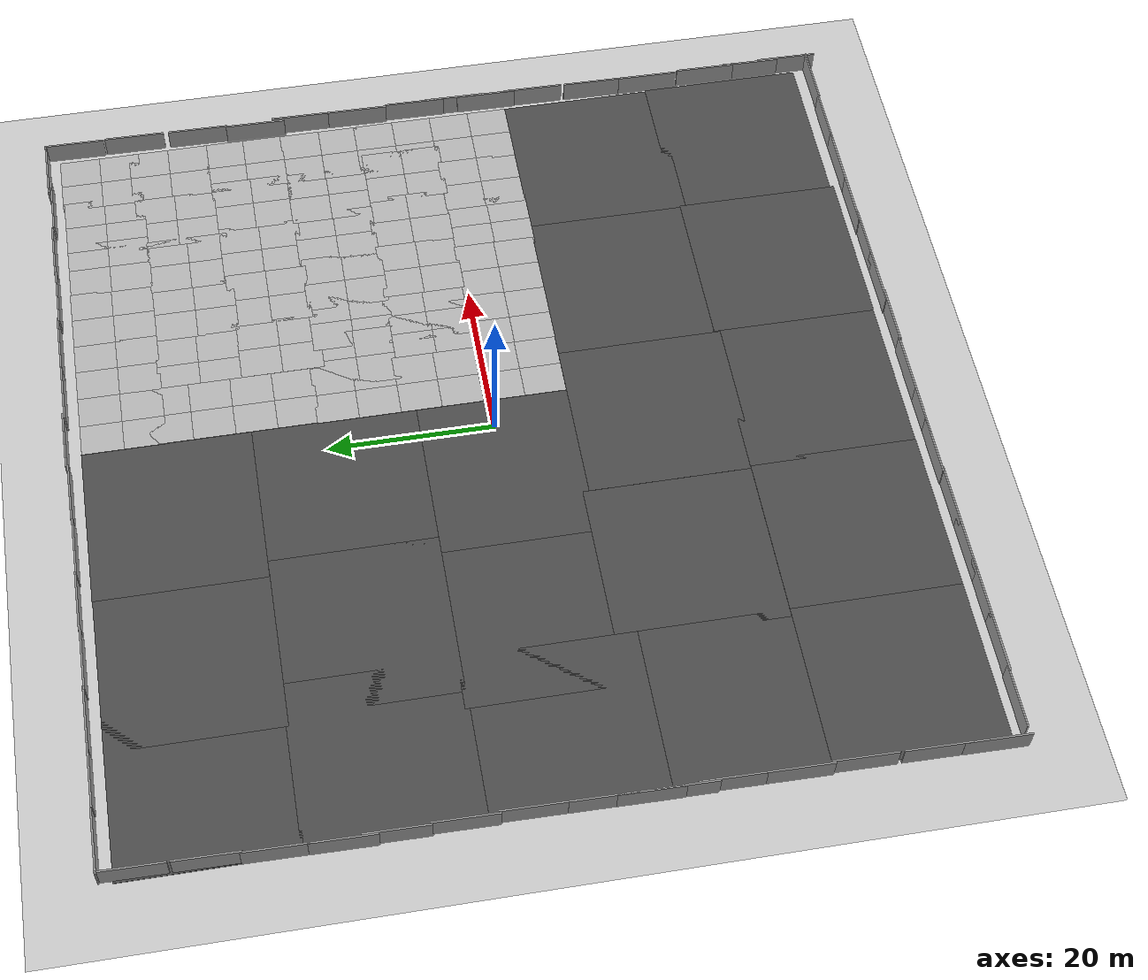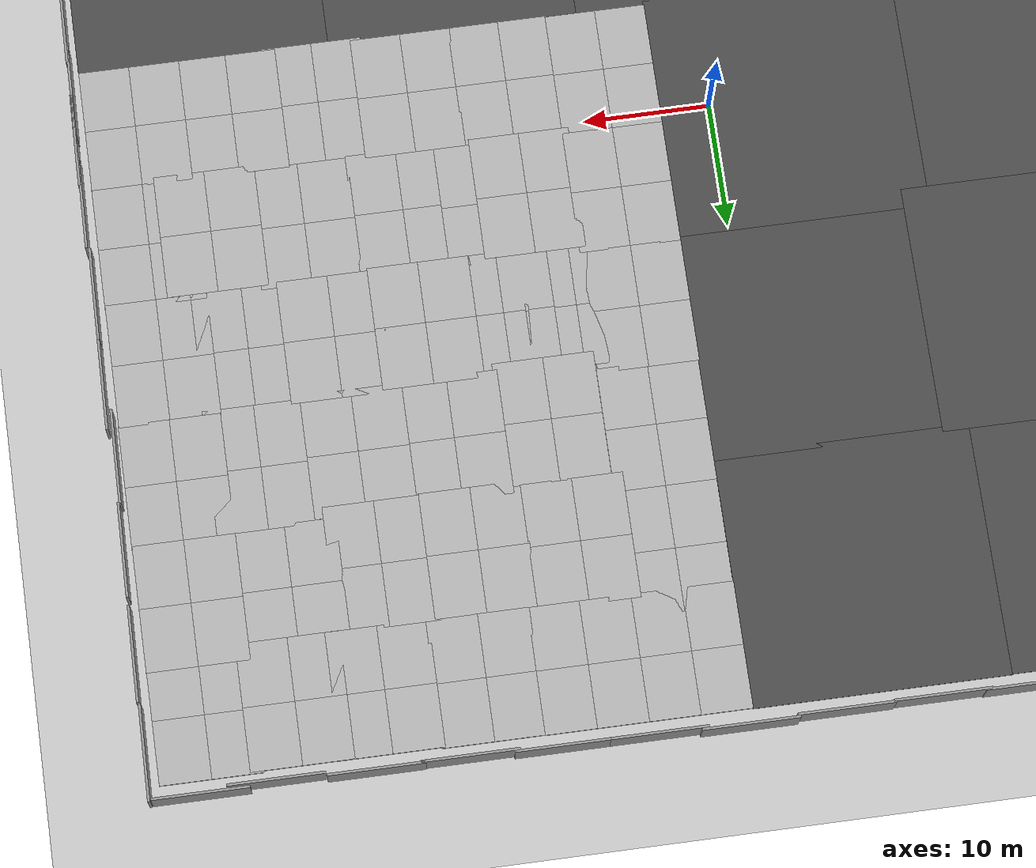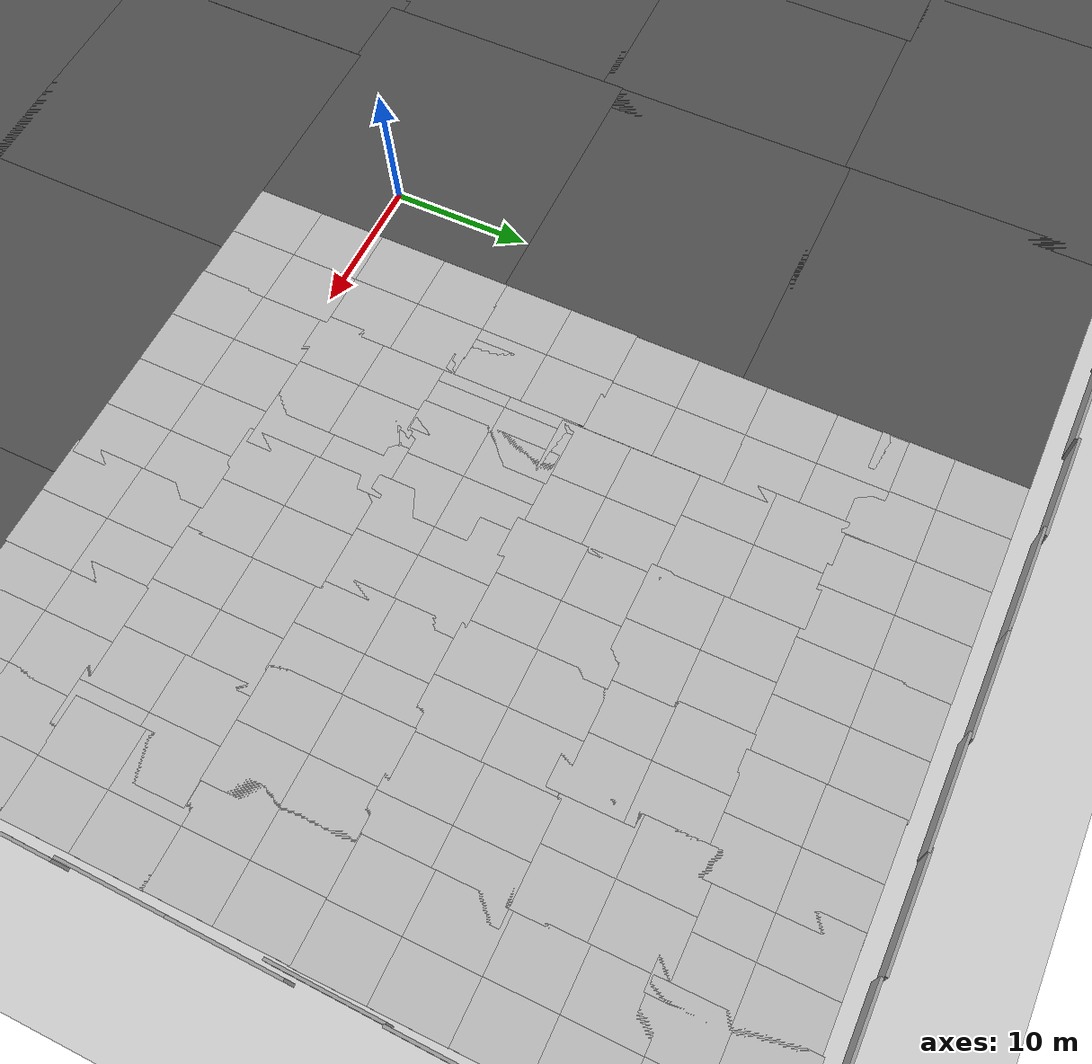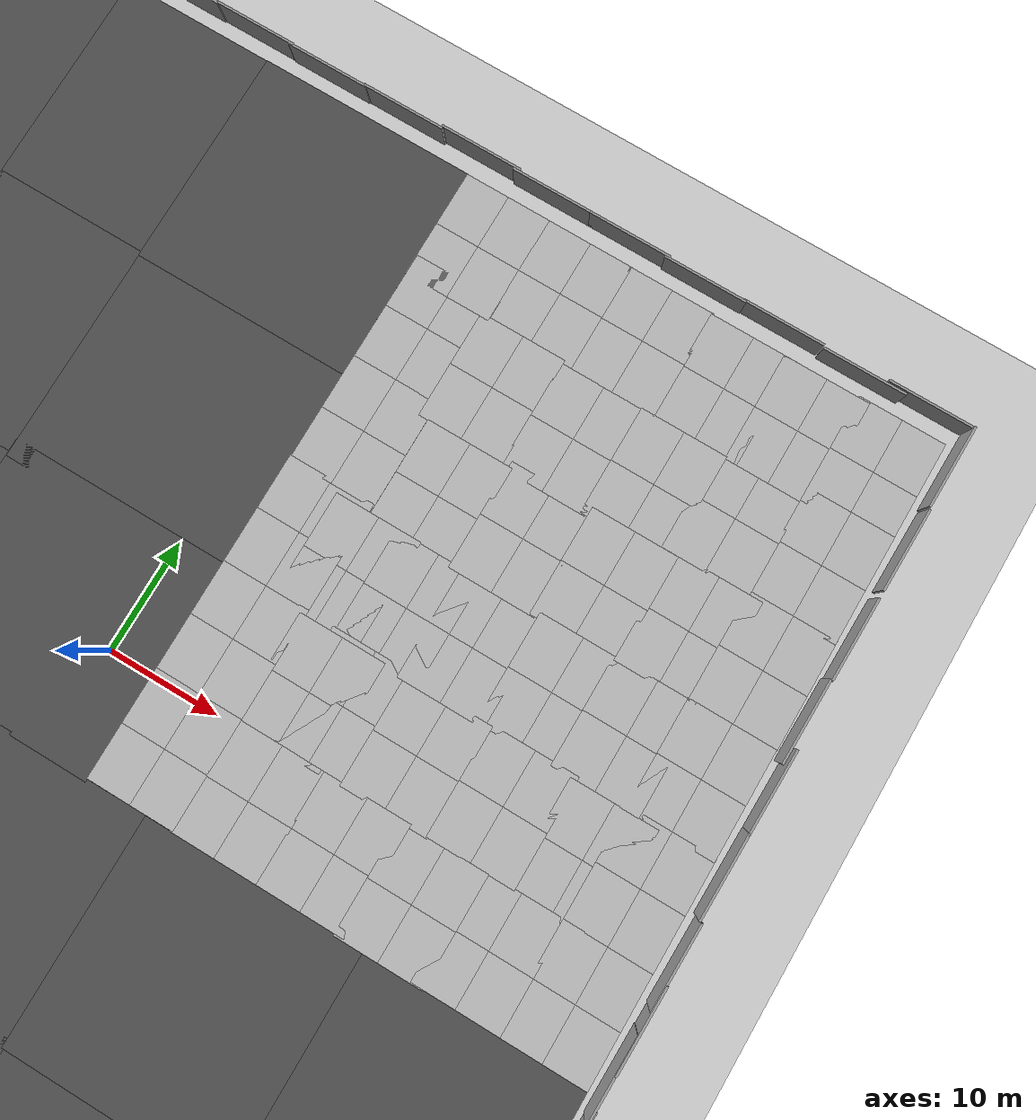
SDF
<sdf version="1.6">
 <world name="default">
  <light name="sun" type="directional">
   <pose>0 0 10 0 -0 0</pose>
   <diffuse>0.8 0.8 0.8 1</diffuse>
   <specular>0.2 0.2 0.2 1</specular>
   <attenuation>
    <range>1000</range>
    <constant>0.9</constant>
    <linear>0.01</linear>
    <quadratic>0.001</quadratic>
   </attenuation>
   <direction>-0.5 0.1 -0.9</direction>
  </light>
  <gravity>0 0 -9.8</gravity>
  <magnetic_field>6e-06 2.3e-05 -4.2e-05</magnetic_field>
  <atmosphere type="adiabatic"/>
  <physics name="default_physics" default="0" type="ode">
   <max_step_size>0.001</max_step_size>
   <real_time_factor>1</real_time_factor>
   <real_time_update_rate>1000</real_time_update_rate>
  </physics>
  <scene><ambient>0.4 0.4 0.4 1</ambient><background>0.7 0.7 0.7 1</background><shadows>1</shadows></scene>
  <audio><device>default</device></audio>
  <spherical_coordinates>
   <surface_model>EARTH_WGS84</surface_model>
   <latitude_deg>0</latitude_deg>
   <longitude_deg>0</longitude_deg>
   <elevation>0</elevation>
   <heading_deg>0</heading_deg>
  </spherical_coordinates>
  <model name="mud_box_clone_1">
   <static>1</static>
   <link name="link">
    <collision name="collision"><geometry><box><size>8 10 0.2</size></box></geometry></collision>
    <visual name="visual_1">
     <pose>-2 2.5 0 0 -0 0</pose>
     <cast_shadows>0</cast_shadows>
     <geometry><box><size>4 5 0.2</size></box></geometry>
     <material>
      <script>
       <uri>model://mud_box/materials/scripts</uri>
       <uri>model://mud_box/materials/textures</uri>
       <name>vrc/mud</name>
      </script>
     </material>
    </visual>
    <visual name="visual_2">
     <pose>2 2.5 0 0 -0 0</pose>
     <cast_shadows>0</cast_shadows>
     <geometry><box><size>4 5 0.2</size></box></geometry>
     <material>
      <script>
       <uri>model://mud_box/materials/scripts</uri>
       <uri>model://mud_box/materials/textures</uri>
       <name>vrc/mud</name>
      </script>
     </material>
    </visual>
    <visual name="visual_3">
     <pose>2 -2.5 0 0 -0 0</pose>
     <cast_shadows>0</cast_shadows>
     <geometry><box><size>4 5 0.2</size></box></geometry>
     <material>
      <script>
       <uri>model://mud_box/materials/scripts</uri>
       <uri>model://mud_box/materials/textures</uri>
       <name>vrc/mud</name>
      </script>
     </material>
    </visual>
    <visual name="visual_4">
     <pose>-2 -2.5 0 0 -0 0</pose>
     <cast_shadows>0</cast_shadows>
     <geometry><box><size>4 5 0.2</size></box></geometry>
     <material>
      <script>
       <uri>model://mud_box/materials/scripts</uri>
       <uri>model://mud_box/materials/textures</uri>
       <name>vrc/mud</name>
      </script>
     </material>
    </visual>
   </link>
   <pose>25.1643 5.35355 0 0 -0 0</pose>
  </model>
  <model name="mud_box_clone_2">
   <static>1</static>
   <link name="link">
    <collision name="collision"><geometry><box><size>8 10 0.2</size></box></geometry></collision>
    <visual name="visual_1">
     <pose>-2 2.5 0 0 -0 0</pose>
     <cast_shadows>0</cast_shadows>
     <geometry><box><size>4 5 0.2</size></box></geometry>
     <material>
      <script>
       <uri>model://mud_box/materials/scripts</uri>
       <uri>model://mud_box/materials/textures</uri>
       <name>vrc/mud</name>
      </script>
     </material>
    </visual>
    <visual name="visual_2">
     <pose>2 2.5 0 0 -0 0</pose>
     <cast_shadows>0</cast_shadows>
     <geometry><box><size>4 5 0.2</size></box></geometry>
     <material>
      <script>
       <uri>model://mud_box/materials/scripts</uri>
       <uri>model://mud_box/materials/textures</uri>
       <name>vrc/mud</name>
      </script>
     </material>
    </visual>
    <visual name="visual_3">
     <pose>2 -2.5 0 0 -0 0</pose>
     <cast_shadows>0</cast_shadows>
     <geometry><box><size>4 5 0.2</size></box></geometry>
     <material>
      <script>
       <uri>model://mud_box/materials/scripts</uri>
       <uri>model://mud_box/materials/textures</uri>
       <name>vrc/mud</name>
      </script>
     </material>
    </visual>
    <visual name="visual_4">
     <pose>-2 -2.5 0 0 -0 0</pose>
     <cast_shadows>0</cast_shadows>
     <geometry><box><size>4 5 0.2</size></box></geometry>
     <material>
      <script>
       <uri>model://mud_box/materials/scripts</uri>
       <uri>model://mud_box/materials/textures</uri>
       <name>vrc/mud</name>
      </script>
     </material>
    </visual>
   </link>
   <pose>33 5.46909 0 0 -0 0</pose>
  </model>
  <model name="mud_box_clone_3">
   <static>1</static>
   <link name="link">
    <collision name="collision"><geometry><box><size>8 10 0.2</size></box></geometry></collision>
    <visual name="visual_1">
     <pose>-2 2.5 0 0 -0 0</pose>
     <cast_shadows>0</cast_shadows>
     <geometry><box><size>4 5 0.2</size></box></geometry>
     <material>
      <script>
       <uri>model://mud_box/materials/scripts</uri>
       <uri>model://mud_box/materials/textures</uri>
       <name>vrc/mud</name>
      </script>
     </material>
    </visual>
    <visual name="visual_2">
     <pose>2 2.5 0 0 -0 0</pose>
     <cast_shadows>0</cast_shadows>
     <geometry><box><size>4 5 0.2</size></box></geometry>
     <material>
      <script>
       <uri>model://mud_box/materials/scripts</uri>
       <uri>model://mud_box/materials/textures</uri>
       <name>vrc/mud</name>
      </script>
     </material>
    </visual>
    <visual name="visual_3">
     <pose>2 -2.5 0 0 -0 0</pose>
     <cast_shadows>0</cast_shadows>
     <geometry><box><size>4 5 0.2</size></box></geometry>
     <material>
      <script>
       <uri>model://mud_box/materials/scripts</uri>
       <uri>model://mud_box/materials/textures</uri>
       <name>vrc/mud</name>
      </script>
     </material>
    </visual>
    <visual name="visual_4">
     <pose>-2 -2.5 0 0 -0 0</pose>
     <cast_shadows>0</cast_shadows>
     <geometry><box><size>4 5 0.2</size></box></geometry>
     <material>
      <script>
       <uri>model://mud_box/materials/scripts</uri>
       <uri>model://mud_box/materials/textures</uri>
       <name>vrc/mud</name>
      </script>
     </material>
    </visual>
   </link>
   <pose>37.5888 -4.36633 0 0 -0 0</pose>
  </model>
  <model name="mud_box_clone_4">
   <static>1</static>
   <link name="link">
    <collision name="collision"><geometry><box><size>8 10 0.2</size></box></geometry></collision>
    <visual name="visual_1">
     <pose>-2 2.5 0 0 -0 0</pose>
     <cast_shadows>0</cast_shadows>
     <geometry><box><size>4 5 0.2</size></box></geometry>
     <material>
      <script>
       <uri>model://mud_box/materials/scripts</uri>
       <uri>model://mud_box/materials/textures</uri>
       <name>vrc/mud</name>
      </script>
     </material>
    </visual>
    <visual name="visual_2">
     <pose>2 2.5 0 0 -0 0</pose>
     <cast_shadows>0</cast_shadows>
     <geometry><box><size>4 5 0.2</size></box></geometry>
     <material>
      <script>
       <uri>model://mud_box/materials/scripts</uri>
       <uri>model://mud_box/materials/textures</uri>
       <name>vrc/mud</name>
      </script>
     </material>
    </visual>
    <visual name="visual_3">
     <pose>2 -2.5 0 0 -0 0</pose>
     <cast_shadows>0</cast_shadows>
     <geometry><box><size>4 5 0.2</size></box></geometry>
     <material>
      <script>
       <uri>model://mud_box/materials/scripts</uri>
       <uri>model://mud_box/materials/textures</uri>
       <name>vrc/mud</name>
      </script>
     </material>
    </visual>
    <visual name="visual_4">
     <pose>-2 -2.5 0 0 -0 0</pose>
     <cast_shadows>0</cast_shadows>
     <geometry><box><size>4 5 0.2</size></box></geometry>
     <material>
      <script>
       <uri>model://mud_box/materials/scripts</uri>
       <uri>model://mud_box/materials/textures</uri>
       <name>vrc/mud</name>
      </script>
     </material>
    </visual>
   </link>
   <pose>45.301 -4.3748 0 0 -0 0</pose>
  </model>
  <model name="mud_box_clone_5">
   <static>1</static>
   <link name="link">
    <collision name="collision"><geometry><box><size>8 10 0.2</size></box></geometry></collision>
    <visual name="visual_1">
     <pose>-2 2.5 0 0 -0 0</pose>
     <cast_shadows>0</cast_shadows>
     <geometry><box><size>4 5 0.2</size></box></geometry>
     <material>
      <script>
       <uri>model://mud_box/materials/scripts</uri>
       <uri>model://mud_box/materials/textures</uri>
       <name>vrc/mud</name>
      </script>
     </material>
    </visual>
    <visual name="visual_2">
     <pose>2 2.5 0 0 -0 0</pose>
     <cast_shadows>0</cast_shadows>
     <geometry><box><size>4 5 0.2</size></box></geometry>
     <material>
      <script>
       <uri>model://mud_box/materials/scripts</uri>
       <uri>model://mud_box/materials/textures</uri>
       <name>vrc/mud</name>
      </script>
     </material>
    </visual>
    <visual name="visual_3">
     <pose>2 -2.5 0 0 -0 0</pose>
     <cast_shadows>0</cast_shadows>
     <geometry><box><size>4 5 0.2</size></box></geometry>
     <material>
      <script>
       <uri>model://mud_box/materials/scripts</uri>
       <uri>model://mud_box/materials/textures</uri>
       <name>vrc/mud</name>
      </script>
     </material>
    </visual>
    <visual name="visual_4">
     <pose>-2 -2.5 0 0 -0 0</pose>
     <cast_shadows>0</cast_shadows>
     <geometry><box><size>4 5 0.2</size></box></geometry>
     <material>
      <script>
       <uri>model://mud_box/materials/scripts</uri>
       <uri>model://mud_box/materials/textures</uri>
       <name>vrc/mud</name>
      </script>
     </material>
    </visual>
   </link>
   <pose>40.378 5.12316 0 0 -0 0</pose>
  </model>
  <model name="mud_box_clone_6">
   <static>1</static>
   <link name="link">
    <collision name="collision"><geometry><box><size>8 10 0.2</size></box></geometry></collision>
    <visual name="visual_1">
     <pose>-2 2.5 0 0 -0 0</pose>
     <cast_shadows>0</cast_shadows>
     <geometry><box><size>4 5 0.2</size></box></geometry>
     <material>
      <script>
       <uri>model://mud_box/materials/scripts</uri>
       <uri>model://mud_box/materials/textures</uri>
       <name>vrc/mud</name>
      </script>
     </material>
    </visual>
    <visual name="visual_2">
     <pose>2 2.5 0 0 -0 0</pose>
     <cast_shadows>0</cast_shadows>
     <geometry><box><size>4 5 0.2</size></box></geometry>
     <material>
      <script>
       <uri>model://mud_box/materials/scripts</uri>
       <uri>model://mud_box/materials/textures</uri>
       <name>vrc/mud</name>
      </script>
     </material>
    </visual>
    <visual name="visual_3">
     <pose>2 -2.5 0 0 -0 0</pose>
     <cast_shadows>0</cast_shadows>
     <geometry><box><size>4 5 0.2</size></box></geometry>
     <material>
      <script>
       <uri>model://mud_box/materials/scripts</uri>
       <uri>model://mud_box/materials/textures</uri>
       <name>vrc/mud</name>
      </script>
     </material>
    </visual>
    <visual name="visual_4">
     <pose>-2 -2.5 0 0 -0 0</pose>
     <cast_shadows>0</cast_shadows>
     <geometry><box><size>4 5 0.2</size></box></geometry>
     <material>
      <script>
       <uri>model://mud_box/materials/scripts</uri>
       <uri>model://mud_box/materials/textures</uri>
       <name>vrc/mud</name>
      </script>
     </material>
    </visual>
   </link>
   <pose>45.3176 5.55034 0 0 -0 0</pose>
  </model>
  <model name="mud_box_clone_7">
   <static>1</static>
   <link name="link">
    <collision name="collision"><geometry><box><size>8 10 0.2</size></box></geometry></collision>
    <visual name="visual_1">
     <pose>-2 2.5 0 0 -0 0</pose>
     <cast_shadows>0</cast_shadows>
     <geometry><box><size>4 5 0.2</size></box></geometry>
     <material>
      <script>
       <uri>model://mud_box/materials/scripts</uri>
       <uri>model://mud_box/materials/textures</uri>
       <name>vrc/mud</name>
      </script>
     </material>
    </visual>
    <visual name="visual_2">
     <pose>2 2.5 0 0 -0 0</pose>
     <cast_shadows>0</cast_shadows>
     <geometry><box><size>4 5 0.2</size></box></geometry>
     <material>
      <script>
       <uri>model://mud_box/materials/scripts</uri>
       <uri>model://mud_box/materials/textures</uri>
       <name>vrc/mud</name>
      </script>
     </material>
    </visual>
    <visual name="visual_3">
     <pose>2 -2.5 0 0 -0 0</pose>
     <cast_shadows>0</cast_shadows>
     <geometry><box><size>4 5 0.2</size></box></geometry>
     <material>
      <script>
       <uri>model://mud_box/materials/scripts</uri>
       <uri>model://mud_box/materials/textures</uri>
       <name>vrc/mud</name>
      </script>
     </material>
    </visual>
    <visual name="visual_4">
     <pose>-2 -2.5 0 0 -0 0</pose>
     <cast_shadows>0</cast_shadows>
     <geometry><box><size>4 5 0.2</size></box></geometry>
     <material>
      <script>
       <uri>model://mud_box/materials/scripts</uri>
       <uri>model://mud_box/materials/textures</uri>
       <name>vrc/mud</name>
      </script>
     </material>
    </visual>
   </link>
   <pose>45.2942 15.1476 0 0 -0 0</pose>
  </model>
  <model name="mud_box_clone_8">
   <static>1</static>
   <link name="link">
    <collision name="collision"><geometry><box><size>8 10 0.2</size></box></geometry></collision>
    <visual name="visual_1">
     <pose>-2 2.5 0 0 -0 0</pose>
     <cast_shadows>0</cast_shadows>
     <geometry><box><size>4 5 0.2</size></box></geometry>
     <material>
      <script>
       <uri>model://mud_box/materials/scripts</uri>
       <uri>model://mud_box/materials/textures</uri>
       <name>vrc/mud</name>
      </script>
     </material>
    </visual>
    <visual name="visual_2">
     <pose>2 2.5 0 0 -0 0</pose>
     <cast_shadows>0</cast_shadows>
     <geometry><box><size>4 5 0.2</size></box></geometry>
     <material>
      <script>
       <uri>model://mud_box/materials/scripts</uri>
       <uri>model://mud_box/materials/textures</uri>
       <name>vrc/mud</name>
      </script>
     </material>
    </visual>
    <visual name="visual_3">
     <pose>2 -2.5 0 0 -0 0</pose>
     <cast_shadows>0</cast_shadows>
     <geometry><box><size>4 5 0.2</size></box></geometry>
     <material>
      <script>
       <uri>model://mud_box/materials/scripts</uri>
       <uri>model://mud_box/materials/textures</uri>
       <name>vrc/mud</name>
      </script>
     </material>
    </visual>
    <visual name="visual_4">
     <pose>-2 -2.5 0 0 -0 0</pose>
     <cast_shadows>0</cast_shadows>
     <geometry><box><size>4 5 0.2</size></box></geometry>
     <material>
      <script>
       <uri>model://mud_box/materials/scripts</uri>
       <uri>model://mud_box/materials/textures</uri>
       <name>vrc/mud</name>
      </script>
     </material>
    </visual>
   </link>
   <pose>38.5803 15.0753 0 0 -0 0</pose>
  </model>
  <model name="mud_box_clone_9">
   <static>1</static>
   <link name="link">
    <collision name="collision"><geometry><box><size>8 10 0.2</size></box></geometry></collision>
    <visual name="visual_1">
     <pose>-2 2.5 0 0 -0 0</pose>
     <cast_shadows>0</cast_shadows>
     <geometry><box><size>4 5 0.2</size></box></geometry>
     <material>
      <script>
       <uri>model://mud_box/materials/scripts</uri>
       <uri>model://mud_box/materials/textures</uri>
       <name>vrc/mud</name>
      </script>
     </material>
    </visual>
    <visual name="visual_2">
     <pose>2 2.5 0 0 -0 0</pose>
     <cast_shadows>0</cast_shadows>
     <geometry><box><size>4 5 0.2</size></box></geometry>
     <material>
      <script>
       <uri>model://mud_box/materials/scripts</uri>
       <uri>model://mud_box/materials/textures</uri>
       <name>vrc/mud</name>
      </script>
     </material>
    </visual>
    <visual name="visual_3">
     <pose>2 -2.5 0 0 -0 0</pose>
     <cast_shadows>0</cast_shadows>
     <geometry><box><size>4 5 0.2</size></box></geometry>
     <material>
      <script>
       <uri>model://mud_box/materials/scripts</uri>
       <uri>model://mud_box/materials/textures</uri>
       <name>vrc/mud</name>
      </script>
     </material>
    </visual>
    <visual name="visual_4">
     <pose>-2 -2.5 0 0 -0 0</pose>
     <cast_shadows>0</cast_shadows>
     <geometry><box><size>4 5 0.2</size></box></geometry>
     <material>
      <script>
       <uri>model://mud_box/materials/scripts</uri>
       <uri>model://mud_box/materials/textures</uri>
       <name>vrc/mud</name>
      </script>
     </material>
    </visual>
   </link>
   <pose>31.7971 14.9894 0 0 -0 0</pose>
  </model>
  <model name="mud_box_clone_10">
   <static>1</static>
   <link name="link">
    <collision name="collision"><geometry><box><size>8 10 0.2</size></box></geometry></collision>
    <visual name="visual_1">
     <pose>-2 2.5 0 0 -0 0</pose>
     <cast_shadows>0</cast_shadows>
     <geometry><box><size>4 5 0.2</size></box></geometry>
     <material>
      <script>
       <uri>model://mud_box/materials/scripts</uri>
       <uri>model://mud_box/materials/textures</uri>
       <name>vrc/mud</name>
      </script>
     </material>
    </visual>
    <visual name="visual_2">
     <pose>2 2.5 0 0 -0 0</pose>
     <cast_shadows>0</cast_shadows>
     <geometry><box><size>4 5 0.2</size></box></geometry>
     <material>
      <script>
       <uri>model://mud_box/materials/scripts</uri>
       <uri>model://mud_box/materials/textures</uri>
       <name>vrc/mud</name>
      </script>
     </material>
    </visual>
    <visual name="visual_3">
     <pose>2 -2.5 0 0 -0 0</pose>
     <cast_shadows>0</cast_shadows>
     <geometry><box><size>4 5 0.2</size></box></geometry>
     <material>
      <script>
       <uri>model://mud_box/materials/scripts</uri>
       <uri>model://mud_box/materials/textures</uri>
       <name>vrc/mud</name>
      </script>
     </material>
    </visual>
    <visual name="visual_4">
     <pose>-2 -2.5 0 0 -0 0</pose>
     <cast_shadows>0</cast_shadows>
     <geometry><box><size>4 5 0.2</size></box></geometry>
     <material>
      <script>
       <uri>model://mud_box/materials/scripts</uri>
       <uri>model://mud_box/materials/textures</uri>
       <name>vrc/mud</name>
      </script>
     </material>
    </visual>
   </link>
   <pose>24.6123 14.8055 0 0 -0 0</pose>
  </model>
  <model name="mud_box_clone_11">
   <static>1</static>
   <link name="link">
    <collision name="collision"><geometry><box><size>8 10 0.2</size></box></geometry></collision>
    <visual name="visual_1">
     <pose>-2 2.5 0 0 -0 0</pose>
     <cast_shadows>0</cast_shadows>
     <geometry><box><size>4 5 0.2</size></box></geometry>
     <material>
      <script>
       <uri>model://mud_box/materials/scripts</uri>
       <uri>model://mud_box/materials/textures</uri>
       <name>vrc/mud</name>
      </script>
     </material>
    </visual>
    <visual name="visual_2">
     <pose>2 2.5 0 0 -0 0</pose>
     <cast_shadows>0</cast_shadows>
     <geometry><box><size>4 5 0.2</size></box></geometry>
     <material>
      <script>
       <uri>model://mud_box/materials/scripts</uri>
       <uri>model://mud_box/materials/textures</uri>
       <name>vrc/mud</name>
      </script>
     </material>
    </visual>
    <visual name="visual_3">
     <pose>2 -2.5 0 0 -0 0</pose>
     <cast_shadows>0</cast_shadows>
     <geometry><box><size>4 5 0.2</size></box></geometry>
     <material>
      <script>
       <uri>model://mud_box/materials/scripts</uri>
       <uri>model://mud_box/materials/textures</uri>
       <name>vrc/mud</name>
      </script>
     </material>
    </visual>
    <visual name="visual_4">
     <pose>-2 -2.5 0 0 -0 0</pose>
     <cast_shadows>0</cast_shadows>
     <geometry><box><size>4 5 0.2</size></box></geometry>
     <material>
      <script>
       <uri>model://mud_box/materials/scripts</uri>
       <uri>model://mud_box/materials/textures</uri>
       <name>vrc/mud</name>
      </script>
     </material>
    </visual>
   </link>
   <pose>18.4493 14.8114 0 0 -0 0</pose>
  </model>
  <model name="mud_box_clone_12">
   <static>1</static>
   <link name="link">
    <collision name="collision"><geometry><box><size>8 10 0.2</size></box></geometry></collision>
    <visual name="visual_1">
     <pose>-2 2.5 0 0 -0 0</pose>
     <cast_shadows>0</cast_shadows>
     <geometry><box><size>4 5 0.2</size></box></geometry>
     <material>
      <script>
       <uri>model://mud_box/materials/scripts</uri>
       <uri>model://mud_box/materials/textures</uri>
       <name>vrc/mud</name>
      </script>
     </material>
    </visual>
    <visual name="visual_2">
     <pose>2 2.5 0 0 -0 0</pose>
     <cast_shadows>0</cast_shadows>
     <geometry><box><size>4 5 0.2</size></box></geometry>
     <material>
      <script>
       <uri>model://mud_box/materials/scripts</uri>
       <uri>model://mud_box/materials/textures</uri>
       <name>vrc/mud</name>
      </script>
     </material>
    </visual>
    <visual name="visual_3">
     <pose>2 -2.5 0 0 -0 0</pose>
     <cast_shadows>0</cast_shadows>
     <geometry><box><size>4 5 0.2</size></box></geometry>
     <material>
      <script>
       <uri>model://mud_box/materials/scripts</uri>
       <uri>model://mud_box/materials/textures</uri>
       <name>vrc/mud</name>
      </script>
     </material>
    </visual>
    <visual name="visual_4">
     <pose>-2 -2.5 0 0 -0 0</pose>
     <cast_shadows>0</cast_shadows>
     <geometry><box><size>4 5 0.2</size></box></geometry>
     <material>
      <script>
       <uri>model://mud_box/materials/scripts</uri>
       <uri>model://mud_box/materials/textures</uri>
       <name>vrc/mud</name>
      </script>
     </material>
    </visual>
   </link>
   <pose>12.7203 14.918 0 0 -0 0</pose>
  </model>
  <model name="mud_box_clone_13">
   <static>1</static>
   <link name="link">
    <collision name="collision"><geometry><box><size>8 10 0.2</size></box></geometry></collision>
    <visual name="visual_1">
     <pose>-2 2.5 0 0 -0 0</pose>
     <cast_shadows>0</cast_shadows>
     <geometry><box><size>4 5 0.2</size></box></geometry>
     <material>
      <script>
       <uri>model://mud_box/materials/scripts</uri>
       <uri>model://mud_box/materials/textures</uri>
       <name>vrc/mud</name>
      </script>
     </material>
    </visual>
    <visual name="visual_2">
     <pose>2 2.5 0 0 -0 0</pose>
     <cast_shadows>0</cast_shadows>
     <geometry><box><size>4 5 0.2</size></box></geometry>
     <material>
      <script>
       <uri>model://mud_box/materials/scripts</uri>
       <uri>model://mud_box/materials/textures</uri>
       <name>vrc/mud</name>
      </script>
     </material>
    </visual>
    <visual name="visual_3">
     <pose>2 -2.5 0 0 -0 0</pose>
     <cast_shadows>0</cast_shadows>
     <geometry><box><size>4 5 0.2</size></box></geometry>
     <material>
      <script>
       <uri>model://mud_box/materials/scripts</uri>
       <uri>model://mud_box/materials/textures</uri>
       <name>vrc/mud</name>
      </script>
     </material>
    </visual>
    <visual name="visual_4">
     <pose>-2 -2.5 0 0 -0 0</pose>
     <cast_shadows>0</cast_shadows>
     <geometry><box><size>4 5 0.2</size></box></geometry>
     <material>
      <script>
       <uri>model://mud_box/materials/scripts</uri>
       <uri>model://mud_box/materials/textures</uri>
       <name>vrc/mud</name>
      </script>
     </material>
    </visual>
   </link>
   <pose>45.3466 24.9799 0 0 -0 0</pose>
  </model>
  <model name="mud_box_clone_14">
   <static>1</static>
   <link name="link">
    <collision name="collision"><geometry><box><size>8 10 0.2</size></box></geometry></collision>
    <visual name="visual_1">
     <pose>-2 2.5 0 0 -0 0</pose>
     <cast_shadows>0</cast_shadows>
     <geometry><box><size>4 5 0.2</size></box></geometry>
     <material>
      <script>
       <uri>model://mud_box/materials/scripts</uri>
       <uri>model://mud_box/materials/textures</uri>
       <name>vrc/mud</name>
      </script>
     </material>
    </visual>
    <visual name="visual_2">
     <pose>2 2.5 0 0 -0 0</pose>
     <cast_shadows>0</cast_shadows>
     <geometry><box><size>4 5 0.2</size></box></geometry>
     <material>
      <script>
       <uri>model://mud_box/materials/scripts</uri>
       <uri>model://mud_box/materials/textures</uri>
       <name>vrc/mud</name>
      </script>
     </material>
    </visual>
    <visual name="visual_3">
     <pose>2 -2.5 0 0 -0 0</pose>
     <cast_shadows>0</cast_shadows>
     <geometry><box><size>4 5 0.2</size></box></geometry>
     <material>
      <script>
       <uri>model://mud_box/materials/scripts</uri>
       <uri>model://mud_box/materials/textures</uri>
       <name>vrc/mud</name>
      </script>
     </material>
    </visual>
    <visual name="visual_4">
     <pose>-2 -2.5 0 0 -0 0</pose>
     <cast_shadows>0</cast_shadows>
     <geometry><box><size>4 5 0.2</size></box></geometry>
     <material>
      <script>
       <uri>model://mud_box/materials/scripts</uri>
       <uri>model://mud_box/materials/textures</uri>
       <name>vrc/mud</name>
      </script>
     </material>
    </visual>
   </link>
   <pose>38.7408 24.6872 0 0 -0 0</pose>
  </model>
  <model name="mud_box_clone_15">
   <static>1</static>
   <link name="link">
    <collision name="collision"><geometry><box><size>8 10 0.2</size></box></geometry></collision>
    <visual name="visual_1">
     <pose>-2 2.5 0 0 -0 0</pose>
     <cast_shadows>0</cast_shadows>
     <geometry><box><size>4 5 0.2</size></box></geometry>
     <material>
      <script>
       <uri>model://mud_box/materials/scripts</uri>
       <uri>model://mud_box/materials/textures</uri>
       <name>vrc/mud</name>
      </script>
     </material>
    </visual>
    <visual name="visual_2">
     <pose>2 2.5 0 0 -0 0</pose>
     <cast_shadows>0</cast_shadows>
     <geometry><box><size>4 5 0.2</size></box></geometry>
     <material>
      <script>
       <uri>model://mud_box/materials/scripts</uri>
       <uri>model://mud_box/materials/textures</uri>
       <name>vrc/mud</name>
      </script>
     </material>
    </visual>
    <visual name="visual_3">
     <pose>2 -2.5 0 0 -0 0</pose>
     <cast_shadows>0</cast_shadows>
     <geometry><box><size>4 5 0.2</size></box></geometry>
     <material>
      <script>
       <uri>model://mud_box/materials/scripts</uri>
       <uri>model://mud_box/materials/textures</uri>
       <name>vrc/mud</name>
      </script>
     </material>
    </visual>
    <visual name="visual_4">
     <pose>-2 -2.5 0 0 -0 0</pose>
     <cast_shadows>0</cast_shadows>
     <geometry><box><size>4 5 0.2</size></box></geometry>
     <material>
      <script>
       <uri>model://mud_box/materials/scripts</uri>
       <uri>model://mud_box/materials/textures</uri>
       <name>vrc/mud</name>
      </script>
     </material>
    </visual>
   </link>
   <pose>31.1182 24.4231 0 0 -0 0</pose>
  </model>
  <model name="mud_box_clone_16">
   <static>1</static>
   <link name="link">
    <collision name="collision"><geometry><box><size>8 10 0.2</size></box></geometry></collision>
    <visual name="visual_1">
     <pose>-2 2.5 0 0 -0 0</pose>
     <cast_shadows>0</cast_shadows>
     <geometry><box><size>4 5 0.2</size></box></geometry>
     <material>
      <script>
       <uri>model://mud_box/materials/scripts</uri>
       <uri>model://mud_box/materials/textures</uri>
       <name>vrc/mud</name>
      </script>
     </material>
    </visual>
    <visual name="visual_2">
     <pose>2 2.5 0 0 -0 0</pose>
     <cast_shadows>0</cast_shadows>
     <geometry><box><size>4 5 0.2</size></box></geometry>
     <material>
      <script>
       <uri>model://mud_box/materials/scripts</uri>
       <uri>model://mud_box/materials/textures</uri>
       <name>vrc/mud</name>
      </script>
     </material>
    </visual>
    <visual name="visual_3">
     <pose>2 -2.5 0 0 -0 0</pose>
     <cast_shadows>0</cast_shadows>
     <geometry><box><size>4 5 0.2</size></box></geometry>
     <material>
      <script>
       <uri>model://mud_box/materials/scripts</uri>
       <uri>model://mud_box/materials/textures</uri>
       <name>vrc/mud</name>
      </script>
     </material>
    </visual>
    <visual name="visual_4">
     <pose>-2 -2.5 0 0 -0 0</pose>
     <cast_shadows>0</cast_shadows>
     <geometry><box><size>4 5 0.2</size></box></geometry>
     <material>
      <script>
       <uri>model://mud_box/materials/scripts</uri>
       <uri>model://mud_box/materials/textures</uri>
       <name>vrc/mud</name>
      </script>
     </material>
    </visual>
   </link>
   <pose>23.6135 24.3316 0 0 -0 0</pose>
  </model>
  <model name="mud_box_clone_17">
   <static>1</static>
   <link name="link">
    <collision name="collision"><geometry><box><size>8 10 0.2</size></box></geometry></collision>
    <visual name="visual_1">
     <pose>-2 2.5 0 0 -0 0</pose>
     <cast_shadows>0</cast_shadows>
     <geometry><box><size>4 5 0.2</size></box></geometry>
     <material>
      <script>
       <uri>model://mud_box/materials/scripts</uri>
       <uri>model://mud_box/materials/textures</uri>
       <name>vrc/mud</name>
      </script>
     </material>
    </visual>
    <visual name="visual_2">
     <pose>2 2.5 0 0 -0 0</pose>
     <cast_shadows>0</cast_shadows>
     <geometry><box><size>4 5 0.2</size></box></geometry>
     <material>
      <script>
       <uri>model://mud_box/materials/scripts</uri>
       <uri>model://mud_box/materials/textures</uri>
       <name>vrc/mud</name>
      </script>
     </material>
    </visual>
    <visual name="visual_3">
     <pose>2 -2.5 0 0 -0 0</pose>
     <cast_shadows>0</cast_shadows>
     <geometry><box><size>4 5 0.2</size></box></geometry>
     <material>
      <script>
       <uri>model://mud_box/materials/scripts</uri>
       <uri>model://mud_box/materials/textures</uri>
       <name>vrc/mud</name>
      </script>
     </material>
    </visual>
    <visual name="visual_4">
     <pose>-2 -2.5 0 0 -0 0</pose>
     <cast_shadows>0</cast_shadows>
     <geometry><box><size>4 5 0.2</size></box></geometry>
     <material>
      <script>
       <uri>model://mud_box/materials/scripts</uri>
       <uri>model://mud_box/materials/textures</uri>
       <name>vrc/mud</name>
      </script>
     </material>
    </visual>
   </link>
   <pose>15.9497 23.8267 0 0 -0 0</pose>
  </model>
  <model name="mud_box_clone_18">
   <static>1</static>
   <link name="link">
    <collision name="collision"><geometry><box><size>8 10 0.2</size></box></geometry></collision>
    <visual name="visual_1">
     <pose>-2 2.5 0 0 -0 0</pose>
     <cast_shadows>0</cast_shadows>
     <geometry><box><size>4 5 0.2</size></box></geometry>
     <material>
      <script>
       <uri>model://mud_box/materials/scripts</uri>
       <uri>model://mud_box/materials/textures</uri>
       <name>vrc/mud</name>
      </script>
     </material>
    </visual>
    <visual name="visual_2">
     <pose>2 2.5 0 0 -0 0</pose>
     <cast_shadows>0</cast_shadows>
     <geometry><box><size>4 5 0.2</size></box></geometry>
     <material>
      <script>
       <uri>model://mud_box/materials/scripts</uri>
       <uri>model://mud_box/materials/textures</uri>
       <name>vrc/mud</name>
      </script>
     </material>
    </visual>
    <visual name="visual_3">
     <pose>2 -2.5 0 0 -0 0</pose>
     <cast_shadows>0</cast_shadows>
     <geometry><box><size>4 5 0.2</size></box></geometry>
     <material>
      <script>
       <uri>model://mud_box/materials/scripts</uri>
       <uri>model://mud_box/materials/textures</uri>
       <name>vrc/mud</name>
      </script>
     </material>
    </visual>
    <visual name="visual_4">
     <pose>-2 -2.5 0 0 -0 0</pose>
     <cast_shadows>0</cast_shadows>
     <geometry><box><size>4 5 0.2</size></box></geometry>
     <material>
      <script>
       <uri>model://mud_box/materials/scripts</uri>
       <uri>model://mud_box/materials/textures</uri>
       <name>vrc/mud</name>
      </script>
     </material>
    </visual>
   </link>
   <pose>45.3234 34.6666 0 0 -0 0</pose>
  </model>
  <model name="mud_box_clone_19">
   <static>1</static>
   <link name="link">
    <collision name="collision"><geometry><box><size>8 10 0.2</size></box></geometry></collision>
    <visual name="visual_1">
     <pose>-2 2.5 0 0 -0 0</pose>
     <cast_shadows>0</cast_shadows>
     <geometry><box><size>4 5 0.2</size></box></geometry>
     <material>
      <script>
       <uri>model://mud_box/materials/scripts</uri>
       <uri>model://mud_box/materials/textures</uri>
       <name>vrc/mud</name>
      </script>
     </material>
    </visual>
    <visual name="visual_2">
     <pose>2 2.5 0 0 -0 0</pose>
     <cast_shadows>0</cast_shadows>
     <geometry><box><size>4 5 0.2</size></box></geometry>
     <material>
      <script>
       <uri>model://mud_box/materials/scripts</uri>
       <uri>model://mud_box/materials/textures</uri>
       <name>vrc/mud</name>
      </script>
     </material>
    </visual>
    <visual name="visual_3">
     <pose>2 -2.5 0 0 -0 0</pose>
     <cast_shadows>0</cast_shadows>
     <geometry><box><size>4 5 0.2</size></box></geometry>
     <material>
      <script>
       <uri>model://mud_box/materials/scripts</uri>
       <uri>model://mud_box/materials/textures</uri>
       <name>vrc/mud</name>
      </script>
     </material>
    </visual>
    <visual name="visual_4">
     <pose>-2 -2.5 0 0 -0 0</pose>
     <cast_shadows>0</cast_shadows>
     <geometry><box><size>4 5 0.2</size></box></geometry>
     <material>
      <script>
       <uri>model://mud_box/materials/scripts</uri>
       <uri>model://mud_box/materials/textures</uri>
       <name>vrc/mud</name>
      </script>
     </material>
    </visual>
   </link>
   <pose>45.3013 43.4356 0 0 -0 0</pose>
  </model>
  <model name="mud_box_clone_20">
   <static>1</static>
   <link name="link">
    <collision name="collision"><geometry><box><size>8 10 0.2</size></box></geometry></collision>
    <visual name="visual_1">
     <pose>-2 2.5 0 0 -0 0</pose>
     <cast_shadows>0</cast_shadows>
     <geometry><box><size>4 5 0.2</size></box></geometry>
     <material>
      <script>
       <uri>model://mud_box/materials/scripts</uri>
       <uri>model://mud_box/materials/textures</uri>
       <name>vrc/mud</name>
      </script>
     </material>
    </visual>
    <visual name="visual_2">
     <pose>2 2.5 0 0 -0 0</pose>
     <cast_shadows>0</cast_shadows>
     <geometry><box><size>4 5 0.2</size></box></geometry>
     <material>
      <script>
       <uri>model://mud_box/materials/scripts</uri>
       <uri>model://mud_box/materials/textures</uri>
       <name>vrc/mud</name>
      </script>
     </material>
    </visual>
    <visual name="visual_3">
     <pose>2 -2.5 0 0 -0 0</pose>
     <cast_shadows>0</cast_shadows>
     <geometry><box><size>4 5 0.2</size></box></geometry>
     <material>
      <script>
       <uri>model://mud_box/materials/scripts</uri>
       <uri>model://mud_box/materials/textures</uri>
       <name>vrc/mud</name>
      </script>
     </material>
    </visual>
    <visual name="visual_4">
     <pose>-2 -2.5 0 0 -0 0</pose>
     <cast_shadows>0</cast_shadows>
     <geometry><box><size>4 5 0.2</size></box></geometry>
     <material>
      <script>
       <uri>model://mud_box/materials/scripts</uri>
       <uri>model://mud_box/materials/textures</uri>
       <name>vrc/mud</name>
      </script>
     </material>
    </visual>
   </link>
   <pose>38.3671 43.3008 0 0 -0 0</pose>
  </model>
  <model name="mud_box_clone_21">
   <static>1</static>
   <link name="link">
    <collision name="collision"><geometry><box><size>8 10 0.2</size></box></geometry></collision>
    <visual name="visual_1">
     <pose>-2 2.5 0 0 -0 0</pose>
     <cast_shadows>0</cast_shadows>
     <geometry><box><size>4 5 0.2</size></box></geometry>
     <material>
      <script>
       <uri>model://mud_box/materials/scripts</uri>
       <uri>model://mud_box/materials/textures</uri>
       <name>vrc/mud</name>
      </script>
     </material>
    </visual>
    <visual name="visual_2">
     <pose>2 2.5 0 0 -0 0</pose>
     <cast_shadows>0</cast_shadows>
     <geometry><box><size>4 5 0.2</size></box></geometry>
     <material>
      <script>
       <uri>model://mud_box/materials/scripts</uri>
       <uri>model://mud_box/materials/textures</uri>
       <name>vrc/mud</name>
      </script>
     </material>
    </visual>
    <visual name="visual_3">
     <pose>2 -2.5 0 0 -0 0</pose>
     <cast_shadows>0</cast_shadows>
     <geometry><box><size>4 5 0.2</size></box></geometry>
     <material>
      <script>
       <uri>model://mud_box/materials/scripts</uri>
       <uri>model://mud_box/materials/textures</uri>
       <name>vrc/mud</name>
      </script>
     </material>
    </visual>
    <visual name="visual_4">
     <pose>-2 -2.5 0 0 -0 0</pose>
     <cast_shadows>0</cast_shadows>
     <geometry><box><size>4 5 0.2</size></box></geometry>
     <material>
      <script>
       <uri>model://mud_box/materials/scripts</uri>
       <uri>model://mud_box/materials/textures</uri>
       <name>vrc/mud</name>
      </script>
     </material>
    </visual>
   </link>
   <pose>31.4757 43.3123 0 0 -0 0</pose>
  </model>
  <model name="mud_box_clone_22">
   <static>1</static>
   <link name="link">
    <collision name="collision"><geometry><box><size>8 10 0.2</size></box></geometry></collision>
    <visual name="visual_1">
     <pose>-2 2.5 0 0 -0 0</pose>
     <cast_shadows>0</cast_shadows>
     <geometry><box><size>4 5 0.2</size></box></geometry>
     <material>
      <script>
       <uri>model://mud_box/materials/scripts</uri>
       <uri>model://mud_box/materials/textures</uri>
       <name>vrc/mud</name>
      </script>
     </material>
    </visual>
    <visual name="visual_2">
     <pose>2 2.5 0 0 -0 0</pose>
     <cast_shadows>0</cast_shadows>
     <geometry><box><size>4 5 0.2</size></box></geometry>
     <material>
      <script>
       <uri>model://mud_box/materials/scripts</uri>
       <uri>model://mud_box/materials/textures</uri>
       <name>vrc/mud</name>
      </script>
     </material>
    </visual>
    <visual name="visual_3">
     <pose>2 -2.5 0 0 -0 0</pose>
     <cast_shadows>0</cast_shadows>
     <geometry><box><size>4 5 0.2</size></box></geometry>
     <material>
      <script>
       <uri>model://mud_box/materials/scripts</uri>
       <uri>model://mud_box/materials/textures</uri>
       <name>vrc/mud</name>
      </script>
     </material>
    </visual>
    <visual name="visual_4">
     <pose>-2 -2.5 0 0 -0 0</pose>
     <cast_shadows>0</cast_shadows>
     <geometry><box><size>4 5 0.2</size></box></geometry>
     <material>
      <script>
       <uri>model://mud_box/materials/scripts</uri>
       <uri>model://mud_box/materials/textures</uri>
       <name>vrc/mud</name>
      </script>
     </material>
    </visual>
   </link>
   <pose>30.4757 33.5146 0 0 -0 0</pose>
  </model>
  <model name="mud_box_clone_23">
   <static>1</static>
   <link name="link">
    <collision name="collision"><geometry><box><size>8 10 0.2</size></box></geometry></collision>
    <visual name="visual_1">
     <pose>-2 2.5 0 0 -0 0</pose>
     <cast_shadows>0</cast_shadows>
     <geometry><box><size>4 5 0.2</size></box></geometry>
     <material>
      <script>
       <uri>model://mud_box/materials/scripts</uri>
       <uri>model://mud_box/materials/textures</uri>
       <name>vrc/mud</name>
      </script>
     </material>
    </visual>
    <visual name="visual_2">
     <pose>2 2.5 0 0 -0 0</pose>
     <cast_shadows>0</cast_shadows>
     <geometry><box><size>4 5 0.2</size></box></geometry>
     <material>
      <script>
       <uri>model://mud_box/materials/scripts</uri>
       <uri>model://mud_box/materials/textures</uri>
       <name>vrc/mud</name>
      </script>
     </material>
    </visual>
    <visual name="visual_3">
     <pose>2 -2.5 0 0 -0 0</pose>
     <cast_shadows>0</cast_shadows>
     <geometry><box><size>4 5 0.2</size></box></geometry>
     <material>
      <script>
       <uri>model://mud_box/materials/scripts</uri>
       <uri>model://mud_box/materials/textures</uri>
       <name>vrc/mud</name>
      </script>
     </material>
    </visual>
    <visual name="visual_4">
     <pose>-2 -2.5 0 0 -0 0</pose>
     <cast_shadows>0</cast_shadows>
     <geometry><box><size>4 5 0.2</size></box></geometry>
     <material>
      <script>
       <uri>model://mud_box/materials/scripts</uri>
       <uri>model://mud_box/materials/textures</uri>
       <name>vrc/mud</name>
      </script>
     </material>
    </visual>
   </link>
   <pose>22.9677 33.4226 0 0 -0 0</pose>
  </model>
  <model name="ground_plane">
   <static>1</static>
   <link name="link">
    <collision name="collision">
     <geometry><plane><normal>0 0 1</normal><size>100 100</size></plane></geometry>
     <surface><friction><ode><mu>100</mu><mu2>50</mu2></ode></friction></surface>
    </collision>
    <visual name="visual">
     <cast_shadows>0</cast_shadows>
     <geometry><plane><normal>0 0 1</normal><size>100 100</size></plane></geometry>
     <material>
      <script><uri>file://media/materials/scripts/gazebo.material</uri><name>Gazebo/Grey</name></script>
     </material>
    </visual>
   </link>
  </model>
  <model name="grey_wall">
   <static>1</static>
   <link name="link">
    <pose>0 0 1.4 0 -0 0</pose>
    <collision name="collision"><geometry><box><size>7.5 0.2 2.8</size></box></geometry></collision>
    <visual name="visual">
     <cast_shadows>0</cast_shadows>
     <geometry><box><size>7.5 0.2 2.8</size></box></geometry>
     <material>
      <script>
       <uri>model://grey_wall/materials/scripts</uri>
       <uri>model://grey_wall/materials/textures</uri>
       <name>vrc/grey_wall</name>
      </script>
     </material>
    </visual>
   </link>
   <pose>-46.1701 49.8815 0 0 -0 0</pose>
  </model>
  <model name="grey_wall_clone">
   <static>1</static>
   <link name="link">
    <pose>0 0 1.4 0 -0 0</pose>
    <collision name="collision"><geometry><box><size>7.5 0.2 2.8</size></box></geometry></collision>
    <visual name="visual">
     <cast_shadows>0</cast_shadows>
     <geometry><box><size>7.5 0.2 2.8</size></box></geometry>
     <material>
      <script>
       <uri>model://grey_wall/materials/scripts</uri>
       <uri>model://grey_wall/materials/textures</uri>
       <name>vrc/grey_wall</name>
      </script>
     </material>
    </visual>
   </link>
   <pose>-38.602 49.801 0 0 -0 0</pose>
  </model>
  <model name="grey_wall_clone_0">
   <static>1</static>
   <link name="link">
    <pose>0 0 1.4 0 -0 0</pose>
    <collision name="collision"><geometry><box><size>7.5 0.2 2.8</size></box></geometry></collision>
    <visual name="visual">
     <cast_shadows>0</cast_shadows>
     <geometry><box><size>7.5 0.2 2.8</size></box></geometry>
     <material>
      <script>
       <uri>model://grey_wall/materials/scripts</uri>
       <uri>model://grey_wall/materials/textures</uri>
       <name>vrc/grey_wall</name>
      </script>
     </material>
    </visual>
   </link>
   <pose>-31.7598 49.801 0 0 -0 0</pose>
  </model>
  <model name="grey_wall_clone_1">
   <static>1</static>
   <link name="link">
    <pose>0 0 1.4 0 -0 0</pose>
    <collision name="collision"><geometry><box><size>7.5 0.2 2.8</size></box></geometry></collision>
    <visual name="visual">
     <cast_shadows>0</cast_shadows>
     <geometry><box><size>7.5 0.2 2.8</size></box></geometry>
     <material>
      <script>
       <uri>model://grey_wall/materials/scripts</uri>
       <uri>model://grey_wall/materials/textures</uri>
       <name>vrc/grey_wall</name>
      </script>
     </material>
    </visual>
   </link>
   <pose>-24.6744 49.7204 0 0 -0 0</pose>
  </model>
  <model name="grey_wall_clone_2">
   <static>1</static>
   <link name="link">
    <pose>0 0 1.4 0 -0 0</pose>
    <collision name="collision"><geometry><box><size>7.5 0.2 2.8</size></box></geometry></collision>
    <visual name="visual">
     <cast_shadows>0</cast_shadows>
     <geometry><box><size>7.5 0.2 2.8</size></box></geometry>
     <material>
      <script>
       <uri>model://grey_wall/materials/scripts</uri>
       <uri>model://grey_wall/materials/textures</uri>
       <name>vrc/grey_wall</name>
      </script>
     </material>
    </visual>
   </link>
   <pose>-17.2675 49.801 0 0 -0 0</pose>
  </model>
  <model name="grey_wall_clone_3">
   <static>1</static>
   <link name="link">
    <pose>0 0 1.4 0 -0 0</pose>
    <collision name="collision"><geometry><box><size>7.5 0.2 2.8</size></box></geometry></collision>
    <visual name="visual">
     <cast_shadows>0</cast_shadows>
     <geometry><box><size>7.5 0.2 2.8</size></box></geometry>
     <material>
      <script>
       <uri>model://grey_wall/materials/scripts</uri>
       <uri>model://grey_wall/materials/textures</uri>
       <name>vrc/grey_wall</name>
      </script>
     </material>
    </visual>
   </link>
   <pose>-10.1824 49.7204 0 0 -0 0</pose>
  </model>
  <model name="grey_wall_clone_4">
   <static>1</static>
   <link name="link">
    <pose>0 0 1.4 0 -0 0</pose>
    <collision name="collision"><geometry><box><size>7.5 0.2 2.8</size></box></geometry></collision>
    <visual name="visual">
     <cast_shadows>0</cast_shadows>
     <geometry><box><size>7.5 0.2 2.8</size></box></geometry>
     <material>
      <script>
       <uri>model://grey_wall/materials/scripts</uri>
       <uri>model://grey_wall/materials/textures</uri>
       <name>vrc/grey_wall</name>
      </script>
     </material>
    </visual>
   </link>
   <pose>-2.85569 49.801 0 0 -0 0</pose>
  </model>
  <model name="grey_wall_clone_5">
   <static>1</static>
   <link name="link">
    <pose>0 0 1.4 0 -0 0</pose>
    <collision name="collision"><geometry><box><size>7.5 0.2 2.8</size></box></geometry></collision>
    <visual name="visual">
     <cast_shadows>0</cast_shadows>
     <geometry><box><size>7.5 0.2 2.8</size></box></geometry>
     <material>
      <script>
       <uri>model://grey_wall/materials/scripts</uri>
       <uri>model://grey_wall/materials/textures</uri>
       <name>vrc/grey_wall</name>
      </script>
     </material>
    </visual>
   </link>
   <pose>4.47068 50 0 0 -0 0</pose>
  </model>
  <model name="grey_wall_clone_6">
   <static>1</static>
   <link name="link">
    <pose>0 0 1.4 0 -0 0</pose>
    <collision name="collision"><geometry><box><size>7.5 0.2 2.8</size></box></geometry></collision>
    <visual name="visual">
     <cast_shadows>0</cast_shadows>
     <geometry><box><size>7.5 0.2 2.8</size></box></geometry>
     <material>
      <script>
       <uri>model://grey_wall/materials/scripts</uri>
       <uri>model://grey_wall/materials/textures</uri>
       <name>vrc/grey_wall</name>
      </script>
     </material>
    </visual>
   </link>
   <pose>11.3946 49.801 0 0 -0 0</pose>
  </model>
  <model name="grey_wall_clone_7">
   <static>1</static>
   <link name="link">
    <pose>0 0 1.4 0 -0 0</pose>
    <collision name="collision"><geometry><box><size>7.5 0.2 2.8</size></box></geometry></collision>
    <visual name="visual">
     <cast_shadows>0</cast_shadows>
     <geometry><box><size>7.5 0.2 2.8</size></box></geometry>
     <material>
      <script>
       <uri>model://grey_wall/materials/scripts</uri>
       <uri>model://grey_wall/materials/textures</uri>
       <name>vrc/grey_wall</name>
      </script>
     </material>
    </visual>
   </link>
   <pose>18.6407 49.801 0 0 -0 0</pose>
  </model>
  <model name="grey_wall_clone_8">
   <static>1</static>
   <link name="link">
    <pose>0 0 1.4 0 -0 0</pose>
    <collision name="collision"><geometry><box><size>7.5 0.2 2.8</size></box></geometry></collision>
    <visual name="visual">
     <cast_shadows>0</cast_shadows>
     <geometry><box><size>7.5 0.2 2.8</size></box></geometry>
     <material>
      <script>
       <uri>model://grey_wall/materials/scripts</uri>
       <uri>model://grey_wall/materials/textures</uri>
       <name>vrc/grey_wall</name>
      </script>
     </material>
    </visual>
   </link>
   <pose>25.7254 49.64 0 0 -0 0</pose>
  </model>
  <model name="grey_wall_clone_9">
   <static>1</static>
   <link name="link">
    <pose>0 0 1.4 0 -0 0</pose>
    <collision name="collision"><geometry><box><size>7.5 0.2 2.8</size></box></geometry></collision>
    <visual name="visual">
     <cast_shadows>0</cast_shadows>
     <geometry><box><size>7.5 0.2 2.8</size></box></geometry>
     <material>
      <script>
       <uri>model://grey_wall/materials/scripts</uri>
       <uri>model://grey_wall/materials/textures</uri>
       <name>vrc/grey_wall</name>
      </script>
     </material>
    </visual>
   </link>
   <pose>32.8552 49.7069 0 0 -0 0</pose>
  </model>
  <model name="grey_wall_clone_10">
   <static>1</static>
   <link name="link">
    <pose>0 0 1.4 0 -0 0</pose>
    <collision name="collision"><geometry><box><size>7.5 0.2 2.8</size></box></geometry></collision>
    <visual name="visual">
     <cast_shadows>0</cast_shadows>
     <geometry><box><size>7.5 0.2 2.8</size></box></geometry>
     <material>
      <script>
       <uri>model://grey_wall/materials/scripts</uri>
       <uri>model://grey_wall/materials/textures</uri>
       <name>vrc/grey_wall</name>
      </script>
     </material>
    </visual>
   </link>
   <pose>40.416 49.49 0 0 -0 0</pose>
  </model>
  <model name="grey_wall_clone_11">
   <static>1</static>
   <link name="link">
    <pose>0 0 1.4 0 -0 0</pose>
    <collision name="collision"><geometry><box><size>7.5 0.2 2.8</size></box></geometry></collision>
    <visual name="visual">
     <cast_shadows>0</cast_shadows>
     <geometry><box><size>7.5 0.2 2.8</size></box></geometry>
     <material>
      <script>
       <uri>model://grey_wall/materials/scripts</uri>
       <uri>model://grey_wall/materials/textures</uri>
       <name>vrc/grey_wall</name>
      </script>
     </material>
    </visual>
   </link>
   <pose>46.1603 49.8154 0 0 -0 0</pose>
  </model>
  <model name="grey_wall_clone_12">
   <static>1</static>
   <link name="link">
    <pose>0 0 1.4 0 -0 0</pose>
    <collision name="collision"><geometry><box><size>7.5 0.2 2.8</size></box></geometry></collision>
    <visual name="visual">
     <cast_shadows>0</cast_shadows>
     <geometry><box><size>7.5 0.2 2.8</size></box></geometry>
     <material>
      <script>
       <uri>model://grey_wall/materials/scripts</uri>
       <uri>model://grey_wall/materials/textures</uri>
       <name>vrc/grey_wall</name>
      </script>
     </material>
    </visual>
   </link>
   <pose>-45.5845 -49.5987 0 0 -0 0</pose>
  </model>
  <model name="grey_wall_clone_13">
   <static>1</static>
   <link name="link">
    <pose>0 0 1.4 0 -0 0</pose>
    <collision name="collision"><geometry><box><size>7.5 0.2 2.8</size></box></geometry></collision>
    <visual name="visual">
     <cast_shadows>0</cast_shadows>
     <geometry><box><size>7.5 0.2 2.8</size></box></geometry>
     <material>
      <script>
       <uri>model://grey_wall/materials/scripts</uri>
       <uri>model://grey_wall/materials/textures</uri>
       <name>vrc/grey_wall</name>
      </script>
     </material>
    </visual>
   </link>
   <pose>-38.6647 -49.7032 0 0 -0 0</pose>
  </model>
  <model name="grey_wall_clone_14">
   <static>1</static>
   <link name="link">
    <pose>0 0 1.4 0 -0 0</pose>
    <collision name="collision"><geometry><box><size>7.5 0.2 2.8</size></box></geometry></collision>
    <visual name="visual">
     <cast_shadows>0</cast_shadows>
     <geometry><box><size>7.5 0.2 2.8</size></box></geometry>
     <material>
      <script>
       <uri>model://grey_wall/materials/scripts</uri>
       <uri>model://grey_wall/materials/textures</uri>
       <name>vrc/grey_wall</name>
      </script>
     </material>
    </visual>
   </link>
   <pose>-31.8514 -49.7032 0 0 -0 0</pose>
  </model>
  <model name="grey_wall_clone_15">
   <static>1</static>
   <link name="link">
    <pose>0 0 1.4 0 -0 0</pose>
    <collision name="collision"><geometry><box><size>7.5 0.2 2.8</size></box></geometry></collision>
    <visual name="visual">
     <cast_shadows>0</cast_shadows>
     <geometry><box><size>7.5 0.2 2.8</size></box></geometry>
     <material>
      <script>
       <uri>model://grey_wall/materials/scripts</uri>
       <uri>model://grey_wall/materials/textures</uri>
       <name>vrc/grey_wall</name>
      </script>
     </material>
    </visual>
   </link>
   <pose>-25.8942 -49.7032 0 0 -0 0</pose>
  </model>
  <model name="grey_wall_clone_16">
   <static>1</static>
   <link name="link">
    <pose>0 0 1.4 0 -0 0</pose>
    <collision name="collision"><geometry><box><size>7.5 0.2 2.8</size></box></geometry></collision>
    <visual name="visual">
     <cast_shadows>0</cast_shadows>
     <geometry><box><size>7.5 0.2 2.8</size></box></geometry>
     <material>
      <script>
       <uri>model://grey_wall/materials/scripts</uri>
       <uri>model://grey_wall/materials/textures</uri>
       <name>vrc/grey_wall</name>
      </script>
     </material>
    </visual>
   </link>
   <pose>-19.5089 -49.7032 0 0 -0 0</pose>
  </model>
  <model name="grey_wall_clone_17">
   <static>1</static>
   <link name="link">
    <pose>0 0 1.4 0 -0 0</pose>
    <collision name="collision"><geometry><box><size>7.5 0.2 2.8</size></box></geometry></collision>
    <visual name="visual">
     <cast_shadows>0</cast_shadows>
     <geometry><box><size>7.5 0.2 2.8</size></box></geometry>
     <material>
      <script>
       <uri>model://grey_wall/materials/scripts</uri>
       <uri>model://grey_wall/materials/textures</uri>
       <name>vrc/grey_wall</name>
      </script>
     </material>
    </visual>
   </link>
   <pose>-12.5891 -49.5987 0 0 -0 0</pose>
  </model>
  <model name="grey_wall_clone_18">
   <static>1</static>
   <link name="link">
    <pose>0 0 1.4 0 -0 0</pose>
    <collision name="collision"><geometry><box><size>7.5 0.2 2.8</size></box></geometry></collision>
    <visual name="visual">
     <cast_shadows>0</cast_shadows>
     <geometry><box><size>7.5 0.2 2.8</size></box></geometry>
     <material>
      <script>
       <uri>model://grey_wall/materials/scripts</uri>
       <uri>model://grey_wall/materials/textures</uri>
       <name>vrc/grey_wall</name>
      </script>
     </material>
    </visual>
   </link>
   <pose>-7.05603 -49.5987 0 0 -0 0</pose>
  </model>
  <model name="grey_wall_clone_19">
   <static>1</static>
   <link name="link">
    <pose>0 0 1.4 0 -0 0</pose>
    <collision name="collision"><geometry><box><size>7.5 0.2 2.8</size></box></geometry></collision>
    <visual name="visual">
     <cast_shadows>0</cast_shadows>
     <geometry><box><size>7.5 0.2 2.8</size></box></geometry>
     <material>
      <script>
       <uri>model://grey_wall/materials/scripts</uri>
       <uri>model://grey_wall/materials/textures</uri>
       <name>vrc/grey_wall</name>
      </script>
     </material>
    </visual>
   </link>
   <pose>-0.670774 -49.5987 0 0 -0 0</pose>
  </model>
  <model name="grey_wall_clone_20">
   <static>1</static>
   <link name="link">
    <pose>0 0 1.4 0 -0 0</pose>
    <collision name="collision"><geometry><box><size>7.5 0.2 2.8</size></box></geometry></collision>
    <visual name="visual">
     <cast_shadows>0</cast_shadows>
     <geometry><box><size>7.5 0.2 2.8</size></box></geometry>
     <material>
      <script>
       <uri>model://grey_wall/materials/scripts</uri>
       <uri>model://grey_wall/materials/textures</uri>
       <name>vrc/grey_wall</name>
      </script>
     </material>
    </visual>
   </link>
   <pose>6.56856 -49.7032 0 0 -0 0</pose>
  </model>
  <model name="grey_wall_clone_21">
   <static>1</static>
   <link name="link">
    <pose>0 0 1.4 0 -0 0</pose>
    <collision name="collision"><geometry><box><size>7.5 0.2 2.8</size></box></geometry></collision>
    <visual name="visual">
     <cast_shadows>0</cast_shadows>
     <geometry><box><size>7.5 0.2 2.8</size></box></geometry>
     <material>
      <script>
       <uri>model://grey_wall/materials/scripts</uri>
       <uri>model://grey_wall/materials/textures</uri>
       <name>vrc/grey_wall</name>
      </script>
     </material>
    </visual>
   </link>
   <pose>12.6343 -49.5987 0 0 -0 0</pose>
  </model>
  <model name="grey_wall_clone_22">
   <static>1</static>
   <link name="link">
    <pose>0 0 1.4 0 -0 0</pose>
    <collision name="collision"><geometry><box><size>7.5 0.2 2.8</size></box></geometry></collision>
    <visual name="visual">
     <cast_shadows>0</cast_shadows>
     <geometry><box><size>7.5 0.2 2.8</size></box></geometry>
     <material>
      <script>
       <uri>model://grey_wall/materials/scripts</uri>
       <uri>model://grey_wall/materials/textures</uri>
       <name>vrc/grey_wall</name>
      </script>
     </material>
    </visual>
   </link>
   <pose>19.1299 -49.5987 0 0 -0 0</pose>
  </model>
  <model name="grey_wall_clone_23">
   <static>1</static>
   <link name="link">
    <pose>0 0 1.4 0 -0 0</pose>
    <collision name="collision"><geometry><box><size>7.5 0.2 2.8</size></box></geometry></collision>
    <visual name="visual">
     <cast_shadows>0</cast_shadows>
     <geometry><box><size>7.5 0.2 2.8</size></box></geometry>
     <material>
      <script>
       <uri>model://grey_wall/materials/scripts</uri>
       <uri>model://grey_wall/materials/textures</uri>
       <name>vrc/grey_wall</name>
      </script>
     </material>
    </visual>
   </link>
   <pose>25.1976 -49.4941 0 0 -0 0</pose>
  </model>
  <model name="grey_wall_clone_24">
   <static>1</static>
   <link name="link">
    <pose>0 0 1.4 0 -0 0</pose>
    <collision name="collision"><geometry><box><size>7.5 0.2 2.8</size></box></geometry></collision>
    <visual name="visual">
     <cast_shadows>0</cast_shadows>
     <geometry><box><size>7.5 0.2 2.8</size></box></geometry>
     <material>
      <script>
       <uri>model://grey_wall/materials/scripts</uri>
       <uri>model://grey_wall/materials/textures</uri>
       <name>vrc/grey_wall</name>
      </script>
     </material>
    </visual>
   </link>
   <pose>32.2181 -49.4941 0 0 -0 0</pose>
  </model>
  <model name="grey_wall_clone_25">
   <static>1</static>
   <link name="link">
    <pose>0 0 1.4 0 -0 0</pose>
    <collision name="collision"><geometry><box><size>7.5 0.2 2.8</size></box></geometry></collision>
    <visual name="visual">
     <cast_shadows>0</cast_shadows>
     <geometry><box><size>7.5 0.2 2.8</size></box></geometry>
     <material>
      <script>
       <uri>model://grey_wall/materials/scripts</uri>
       <uri>model://grey_wall/materials/textures</uri>
       <name>vrc/grey_wall</name>
      </script>
     </material>
    </visual>
   </link>
   <pose>38.8183 -49.4941 0 0 -0 0</pose>
  </model>
  <model name="grey_wall_clone_26">
   <static>1</static>
   <link name="link">
    <pose>0 0 1.4 0 -0 0</pose>
    <collision name="collision"><geometry><box><size>7.5 0.2 2.8</size></box></geometry></collision>
    <visual name="visual">
     <cast_shadows>0</cast_shadows>
     <geometry><box><size>7.5 0.2 2.8</size></box></geometry>
     <material>
      <script>
       <uri>model://grey_wall/materials/scripts</uri>
       <uri>model://grey_wall/materials/textures</uri>
       <name>vrc/grey_wall</name>
      </script>
     </material>
    </visual>
   </link>
   <pose>46.2687 -49.5987 0 0 -0 0</pose>
  </model>
  <model name="grey_wall_clone_27">
   <static>1</static>
   <link name="link">
    <pose>0 0 1.4 0 -0 0</pose>
    <collision name="collision"><geometry><box><size>7.5 0.2 2.8</size></box></geometry></collision>
    <visual name="visual">
     <cast_shadows>0</cast_shadows>
     <geometry><box><size>7.5 0.2 2.8</size></box></geometry>
     <material>
      <script>
       <uri>model://grey_wall/materials/scripts</uri>
       <uri>model://grey_wall/materials/textures</uri>
       <name>vrc/grey_wall</name>
      </script>
     </material>
    </visual>
   </link>
   <pose>-49.7193 46.2533 0 0 0 -1.5859</pose>
  </model>
  <model name="grey_wall_clone_27_clone">
   <static>1</static>
   <link name="link">
    <pose>0 0 1.4 0 -0 0</pose>
    <collision name="collision"><geometry><box><size>7.5 0.2 2.8</size></box></geometry></collision>
    <visual name="visual">
     <cast_shadows>0</cast_shadows>
     <geometry><box><size>7.5 0.2 2.8</size></box></geometry>
     <material>
      <script>
       <uri>model://grey_wall/materials/scripts</uri>
       <uri>model://grey_wall/materials/textures</uri>
       <name>vrc/grey_wall</name>
      </script>
     </material>
    </visual>
   </link>
   <pose>-49.815 38.4554 0 0 0 -1.5859</pose>
  </model>
  <model name="grey_wall_clone_27_clone_0">
   <static>1</static>
   <link name="link">
    <pose>0 0 1.4 0 -0 0</pose>
    <collision name="collision"><geometry><box><size>7.5 0.2 2.8</size></box></geometry></collision>
    <visual name="visual">
     <cast_shadows>0</cast_shadows>
     <geometry><box><size>7.5 0.2 2.8</size></box></geometry>
     <material>
      <script>
       <uri>model://grey_wall/materials/scripts</uri>
       <uri>model://grey_wall/materials/textures</uri>
       <name>vrc/grey_wall</name>
      </script>
     </material>
    </visual>
   </link>
   <pose>-50.0316 31.29 0 0 0 -1.5859</pose>
  </model>
  <model name="grey_wall_clone_27_clone_1">
   <static>1</static>
   <link name="link">
    <pose>0 0 1.4 0 -0 0</pose>
    <collision name="collision"><geometry><box><size>7.5 0.2 2.8</size></box></geometry></collision>
    <visual name="visual">
     <cast_shadows>0</cast_shadows>
     <geometry><box><size>7.5 0.2 2.8</size></box></geometry>
     <material>
      <script>
       <uri>model://grey_wall/materials/scripts</uri>
       <uri>model://grey_wall/materials/textures</uri>
       <name>vrc/grey_wall</name>
      </script>
     </material>
    </visual>
   </link>
   <pose>-50.152 24.2369 0 0 0 -1.5859</pose>
  </model>
  <model name="grey_wall_clone_27_clone_2">
   <static>1</static>
   <link name="link">
    <pose>0 0 1.4 0 -0 0</pose>
    <collision name="collision"><geometry><box><size>7.5 0.2 2.8</size></box></geometry></collision>
    <visual name="visual">
     <cast_shadows>0</cast_shadows>
     <geometry><box><size>7.5 0.2 2.8</size></box></geometry>
     <material>
      <script>
       <uri>model://grey_wall/materials/scripts</uri>
       <uri>model://grey_wall/materials/textures</uri>
       <name>vrc/grey_wall</name>
      </script>
     </material>
    </visual>
   </link>
   <pose>-50.0316 18.6161 0 0 0 -1.5859</pose>
  </model>
  <model name="grey_wall_clone_27_clone_3">
   <static>1</static>
   <link name="link">
    <pose>0 0 1.4 0 -0 0</pose>
    <collision name="collision"><geometry><box><size>7.5 0.2 2.8</size></box></geometry></collision>
    <visual name="visual">
     <cast_shadows>0</cast_shadows>
     <geometry><box><size>7.5 0.2 2.8</size></box></geometry>
     <material>
      <script>
       <uri>model://grey_wall/materials/scripts</uri>
       <uri>model://grey_wall/materials/textures</uri>
       <name>vrc/grey_wall</name>
      </script>
     </material>
    </visual>
   </link>
   <pose>-49.9353 11.3383 0 0 0 -1.5859</pose>
  </model>
  <model name="grey_wall_clone_27_clone_4">
   <static>1</static>
   <link name="link">
    <pose>0 0 1.4 0 -0 0</pose>
    <collision name="collision"><geometry><box><size>7.5 0.2 2.8</size></box></geometry></collision>
    <visual name="visual">
     <cast_shadows>0</cast_shadows>
     <geometry><box><size>7.5 0.2 2.8</size></box></geometry>
     <material>
      <script>
       <uri>model://grey_wall/materials/scripts</uri>
       <uri>model://grey_wall/materials/textures</uri>
       <name>vrc/grey_wall</name>
      </script>
     </material>
    </visual>
   </link>
   <pose>-49.815 4.17291 0 0 0 -1.5859</pose>
  </model>
  <model name="grey_wall_clone_27_clone_5">
   <static>1</static>
   <link name="link">
    <pose>0 0 1.4 0 -0 0</pose>
    <collision name="collision"><geometry><box><size>7.5 0.2 2.8</size></box></geometry></collision>
    <visual name="visual">
     <cast_shadows>0</cast_shadows>
     <geometry><box><size>7.5 0.2 2.8</size></box></geometry>
     <material>
      <script>
       <uri>model://grey_wall/materials/scripts</uri>
       <uri>model://grey_wall/materials/textures</uri>
       <name>vrc/grey_wall</name>
      </script>
     </material>
    </visual>
   </link>
   <pose>-49.9353 -3.32151 0 0 0 -1.5859</pose>
  </model>
  <model name="grey_wall_clone_27_clone_6">
   <static>1</static>
   <link name="link">
    <pose>0 0 1.4 0 -0 0</pose>
    <collision name="collision"><geometry><box><size>7.5 0.2 2.8</size></box></geometry></collision>
    <visual name="visual">
     <cast_shadows>0</cast_shadows>
     <geometry><box><size>7.5 0.2 2.8</size></box></geometry>
     <material>
      <script>
       <uri>model://grey_wall/materials/scripts</uri>
       <uri>model://grey_wall/materials/textures</uri>
       <name>vrc/grey_wall</name>
      </script>
     </material>
    </visual>
   </link>
   <pose>-50.0316 -8.50501 0 0 0 -1.5859</pose>
  </model>
  <model name="grey_wall_clone_27_clone_7">
   <static>1</static>
   <link name="link">
    <pose>0 0 1.4 0 -0 0</pose>
    <collision name="collision"><geometry><box><size>7.5 0.2 2.8</size></box></geometry></collision>
    <visual name="visual">
     <cast_shadows>0</cast_shadows>
     <geometry><box><size>7.5 0.2 2.8</size></box></geometry>
     <material>
      <script>
       <uri>model://grey_wall/materials/scripts</uri>
       <uri>model://grey_wall/materials/textures</uri>
       <name>vrc/grey_wall</name>
      </script>
     </material>
    </visual>
   </link>
   <pose>-50.0316 -12.1439 0 0 0 -1.5859</pose>
  </model>
  <model name="grey_wall_clone_27_clone_8">
   <static>1</static>
   <link name="link">
    <pose>0 0 1.4 0 -0 0</pose>
    <collision name="collision"><geometry><box><size>7.5 0.2 2.8</size></box></geometry></collision>
    <visual name="visual">
     <cast_shadows>0</cast_shadows>
     <geometry><box><size>7.5 0.2 2.8</size></box></geometry>
     <material>
      <script>
       <uri>model://grey_wall/materials/scripts</uri>
       <uri>model://grey_wall/materials/textures</uri>
       <name>vrc/grey_wall</name>
      </script>
     </material>
    </visual>
   </link>
   <pose>-49.9353 -17.2151 0 0 0 -1.5859</pose>
  </model>
  <model name="grey_wall_clone_27_clone_9">
   <static>1</static>
   <link name="link">
    <pose>0 0 1.4 0 -0 0</pose>
    <collision name="collision"><geometry><box><size>7.5 0.2 2.8</size></box></geometry></collision>
    <visual name="visual">
     <cast_shadows>0</cast_shadows>
     <geometry><box><size>7.5 0.2 2.8</size></box></geometry>
     <material>
      <script>
       <uri>model://grey_wall/materials/scripts</uri>
       <uri>model://grey_wall/materials/textures</uri>
       <name>vrc/grey_wall</name>
      </script>
     </material>
    </visual>
   </link>
   <pose>-50.0316 -24.6011 0 0 0 -1.5859</pose>
  </model>
  <model name="grey_wall_clone_27_clone_10">
   <static>1</static>
   <link name="link">
    <pose>0 0 1.4 0 -0 0</pose>
    <collision name="collision"><geometry><box><size>7.5 0.2 2.8</size></box></geometry></collision>
    <visual name="visual">
     <cast_shadows>0</cast_shadows>
     <geometry><box><size>7.5 0.2 2.8</size></box></geometry>
     <material>
      <script>
       <uri>model://grey_wall/materials/scripts</uri>
       <uri>model://grey_wall/materials/textures</uri>
       <name>vrc/grey_wall</name>
      </script>
     </material>
    </visual>
   </link>
   <pose>-49.9353 -31.6542 0 0 0 -1.5859</pose>
  </model>
  <model name="grey_wall_clone_27_clone_11">
   <static>1</static>
   <link name="link">
    <pose>0 0 1.4 0 -0 0</pose>
    <collision name="collision"><geometry><box><size>7.5 0.2 2.8</size></box></geometry></collision>
    <visual name="visual">
     <cast_shadows>0</cast_shadows>
     <geometry><box><size>7.5 0.2 2.8</size></box></geometry>
     <material>
      <script>
       <uri>model://grey_wall/materials/scripts</uri>
       <uri>model://grey_wall/materials/textures</uri>
       <name>vrc/grey_wall</name>
      </script>
     </material>
    </visual>
   </link>
   <pose>-50.0316 -39.598 0 0 0 -1.5859</pose>
  </model>
  <model name="grey_wall_clone_27_clone_12">
   <static>1</static>
   <link name="link">
    <pose>0 0 1.4 0 -0 0</pose>
    <collision name="collision"><geometry><box><size>7.5 0.2 2.8</size></box></geometry></collision>
    <visual name="visual">
     <cast_shadows>0</cast_shadows>
     <geometry><box><size>7.5 0.2 2.8</size></box></geometry>
     <material>
      <script>
       <uri>model://grey_wall/materials/scripts</uri>
       <uri>model://grey_wall/materials/textures</uri>
       <name>vrc/grey_wall</name>
      </script>
     </material>
    </visual>
   </link>
   <pose>-50.152 -46.2098 0 0 0 -1.5859</pose>
  </model>
  <model name="grey_wall_clone_27_clone_13">
   <static>1</static>
   <link name="link">
    <pose>0 0 1.4 0 -0 0</pose>
    <collision name="collision"><geometry><box><size>7.5 0.2 2.8</size></box></geometry></collision>
    <visual name="visual">
     <cast_shadows>0</cast_shadows>
     <geometry><box><size>7.5 0.2 2.8</size></box></geometry>
     <material>
      <script>
       <uri>model://grey_wall/materials/scripts</uri>
       <uri>model://grey_wall/materials/textures</uri>
       <name>vrc/grey_wall</name>
      </script>
     </material>
    </visual>
   </link>
   <pose>50.0041 46.2163 0 0 0 -1.5859</pose>
  </model>
  <model name="grey_wall_clone_27_clone_14">
   <static>1</static>
   <link name="link">
    <pose>0 0 1.4 0 -0 0</pose>
    <collision name="collision"><geometry><box><size>7.5 0.2 2.8</size></box></geometry></collision>
    <visual name="visual">
     <cast_shadows>0</cast_shadows>
     <geometry><box><size>7.5 0.2 2.8</size></box></geometry>
     <material>
      <script>
       <uri>model://grey_wall/materials/scripts</uri>
       <uri>model://grey_wall/materials/textures</uri>
       <name>vrc/grey_wall</name>
      </script>
     </material>
    </visual>
   </link>
   <pose>50.0041 38.5851 0 0 0 -1.5859</pose>
  </model>
  <model name="grey_wall_clone_27_clone_15">
   <static>1</static>
   <link name="link">
    <pose>0 0 1.4 0 -0 0</pose>
    <collision name="collision"><geometry><box><size>7.5 0.2 2.8</size></box></geometry></collision>
    <visual name="visual">
     <cast_shadows>0</cast_shadows>
     <geometry><box><size>7.5 0.2 2.8</size></box></geometry>
     <material>
      <script>
       <uri>model://grey_wall/materials/scripts</uri>
       <uri>model://grey_wall/materials/textures</uri>
       <name>vrc/grey_wall</name>
      </script>
     </material>
    </visual>
   </link>
   <pose>49.8903 30.469 0 0 0 -1.5859</pose>
  </model>
  <model name="grey_wall_clone_27_clone_16">
   <static>1</static>
   <link name="link">
    <pose>0 0 1.4 0 -0 0</pose>
    <collision name="collision"><geometry><box><size>7.5 0.2 2.8</size></box></geometry></collision>
    <visual name="visual">
     <cast_shadows>0</cast_shadows>
     <geometry><box><size>7.5 0.2 2.8</size></box></geometry>
     <material>
      <script>
       <uri>model://grey_wall/materials/scripts</uri>
       <uri>model://grey_wall/materials/textures</uri>
       <name>vrc/grey_wall</name>
      </script>
     </material>
    </visual>
   </link>
   <pose>49.6434 23.078 0 0 0 -1.5859</pose>
  </model>
  <model name="grey_wall_clone_27_clone_17">
   <static>1</static>
   <link name="link">
    <pose>0 0 1.4 0 -0 0</pose>
    <collision name="collision"><geometry><box><size>7.5 0.2 2.8</size></box></geometry></collision>
    <visual name="visual">
     <cast_shadows>0</cast_shadows>
     <geometry><box><size>7.5 0.2 2.8</size></box></geometry>
     <material>
      <script>
       <uri>model://grey_wall/materials/scripts</uri>
       <uri>model://grey_wall/materials/textures</uri>
       <name>vrc/grey_wall</name>
      </script>
     </material>
    </visual>
   </link>
   <pose>50.0049 17.1441 0 0 0 -1.5859</pose>
  </model>
  <model name="grey_wall_clone_27_clone_18">
   <static>1</static>
   <link name="link">
    <pose>0 0 1.4 0 -0 0</pose>
    <collision name="collision"><geometry><box><size>7.5 0.2 2.8</size></box></geometry></collision>
    <visual name="visual">
     <cast_shadows>0</cast_shadows>
     <geometry><box><size>7.5 0.2 2.8</size></box></geometry>
     <material>
      <script>
       <uri>model://grey_wall/materials/scripts</uri>
       <uri>model://grey_wall/materials/textures</uri>
       <name>vrc/grey_wall</name>
      </script>
     </material>
    </visual>
   </link>
   <pose>49.8903 9.87447 0 0 0 -1.5859</pose>
  </model>
  <model name="grey_wall_clone_27_clone_19">
   <static>1</static>
   <link name="link">
    <pose>0 0 1.4 0 -0 0</pose>
    <collision name="collision"><geometry><box><size>7.5 0.2 2.8</size></box></geometry></collision>
    <visual name="visual">
     <cast_shadows>0</cast_shadows>
     <geometry><box><size>7.5 0.2 2.8</size></box></geometry>
     <material>
      <script>
       <uri>model://grey_wall/materials/scripts</uri>
       <uri>model://grey_wall/materials/textures</uri>
       <name>vrc/grey_wall</name>
      </script>
     </material>
    </visual>
   </link>
   <pose>50.0049 2.36453 0 0 0 -1.5859</pose>
  </model>
  <model name="grey_wall_clone_27_clone_20">
   <static>1</static>
   <link name="link">
    <pose>0 0 1.4 0 -0 0</pose>
    <collision name="collision"><geometry><box><size>7.5 0.2 2.8</size></box></geometry></collision>
    <visual name="visual">
     <cast_shadows>0</cast_shadows>
     <geometry><box><size>7.5 0.2 2.8</size></box></geometry>
     <material>
      <script>
       <uri>model://grey_wall/materials/scripts</uri>
       <uri>model://grey_wall/materials/textures</uri>
       <name>vrc/grey_wall</name>
      </script>
     </material>
    </visual>
   </link>
   <pose>49.8903 -6.96394 0 0 0 -1.5859</pose>
  </model>
  <model name="grey_wall_clone_27_clone_21">
   <static>1</static>
   <link name="link">
    <pose>0 0 1.4 0 -0 0</pose>
    <collision name="collision"><geometry><box><size>7.5 0.2 2.8</size></box></geometry></collision>
    <visual name="visual">
     <cast_shadows>0</cast_shadows>
     <geometry><box><size>7.5 0.2 2.8</size></box></geometry>
     <material>
      <script>
       <uri>model://grey_wall/materials/scripts</uri>
       <uri>model://grey_wall/materials/textures</uri>
       <name>vrc/grey_wall</name>
      </script>
     </material>
    </visual>
   </link>
   <pose>50.0049 -2.84416 0 0 0 -1.5859</pose>
  </model>
  <model name="grey_wall_clone_27_clone_22">
   <static>1</static>
   <link name="link">
    <pose>0 0 1.4 0 -0 0</pose>
    <collision name="collision"><geometry><box><size>7.5 0.2 2.8</size></box></geometry></collision>
    <visual name="visual">
     <cast_shadows>0</cast_shadows>
     <geometry><box><size>7.5 0.2 2.8</size></box></geometry>
     <material>
      <script>
       <uri>model://grey_wall/materials/scripts</uri>
       <uri>model://grey_wall/materials/textures</uri>
       <name>vrc/grey_wall</name>
      </script>
     </material>
    </visual>
   </link>
   <pose>49.8903 -13.1425 0 0 0 -1.5859</pose>
  </model>
  <model name="grey_wall_clone_27_clone_23">
   <static>1</static>
   <link name="link">
    <pose>0 0 1.4 0 -0 0</pose>
    <collision name="collision"><geometry><box><size>7.5 0.2 2.8</size></box></geometry></collision>
    <visual name="visual">
     <cast_shadows>0</cast_shadows>
     <geometry><box><size>7.5 0.2 2.8</size></box></geometry>
     <material>
      <script>
       <uri>model://grey_wall/materials/scripts</uri>
       <uri>model://grey_wall/materials/textures</uri>
       <name>vrc/grey_wall</name>
      </script>
     </material>
    </visual>
   </link>
   <pose>49.7668 -21.0184 0 0 0 -1.5859</pose>
  </model>
  <model name="grey_wall_clone_27_clone_24">
   <static>1</static>
   <link name="link">
    <pose>0 0 1.4 0 -0 0</pose>
    <collision name="collision"><geometry><box><size>7.5 0.2 2.8</size></box></geometry></collision>
    <visual name="visual">
     <cast_shadows>0</cast_shadows>
     <geometry><box><size>7.5 0.2 2.8</size></box></geometry>
     <material>
      <script>
       <uri>model://grey_wall/materials/scripts</uri>
       <uri>model://grey_wall/materials/textures</uri>
       <name>vrc/grey_wall</name>
      </script>
     </material>
    </visual>
   </link>
   <pose>49.6434 -28.2836 0 0 0 -1.5859</pose>
  </model>
  <model name="grey_wall_clone_27_clone_25">
   <static>1</static>
   <link name="link">
    <pose>0 0 1.4 0 -0 0</pose>
    <collision name="collision"><geometry><box><size>7.5 0.2 2.8</size></box></geometry></collision>
    <visual name="visual">
     <cast_shadows>0</cast_shadows>
     <geometry><box><size>7.5 0.2 2.8</size></box></geometry>
     <material>
      <script>
       <uri>model://grey_wall/materials/scripts</uri>
       <uri>model://grey_wall/materials/textures</uri>
       <name>vrc/grey_wall</name>
      </script>
     </material>
    </visual>
   </link>
   <pose>49.7668 -36.036 0 0 0 -1.5859</pose>
  </model>
  <model name="grey_wall_clone_27_clone_26">
   <static>1</static>
   <link name="link">
    <pose>0 0 1.4 0 -0 0</pose>
    <collision name="collision"><geometry><box><size>7.5 0.2 2.8</size></box></geometry></collision>
    <visual name="visual">
     <cast_shadows>0</cast_shadows>
     <geometry><box><size>7.5 0.2 2.8</size></box></geometry>
     <material>
      <script>
       <uri>model://grey_wall/materials/scripts</uri>
       <uri>model://grey_wall/materials/textures</uri>
       <name>vrc/grey_wall</name>
      </script>
     </material>
    </visual>
   </link>
   <pose>49.7668 -41.9721 0 0 0 -1.5859</pose>
  </model>
  <model name="grey_wall_clone_27_clone_27">
   <static>1</static>
   <link name="link">
    <pose>0 0 1.4 0 -0 0</pose>
    <collision name="collision"><geometry><box><size>7.5 0.2 2.8</size></box></geometry></collision>
    <visual name="visual">
     <cast_shadows>0</cast_shadows>
     <geometry><box><size>7.5 0.2 2.8</size></box></geometry>
     <material>
      <script>
       <uri>model://grey_wall/materials/scripts</uri>
       <uri>model://grey_wall/materials/textures</uri>
       <name>vrc/grey_wall</name>
      </script>
     </material>
    </visual>
   </link>
   <pose>49.8903 -46.9406 0 0 0 -1.5859</pose>
  </model>
  <model name="asphalt_plane_clone">
   <static>1</static>
   <link name="link">
    <collision name="collision"><geometry><box><size>20 20 0.1</size></box></geometry></collision>
    <visual name="visual">
     <cast_shadows>0</cast_shadows>
     <geometry><box><size>20 20 0.1</size></box></geometry>
     <material>
      <script>
       <uri>model://asphalt_plane/materials/scripts</uri>
       <uri>model://asphalt_plane/materials/textures</uri>
       <name>vrc/asphalt</name>
      </script>
     </material>
    </visual>
   </link>
   <pose>-6.06602 38.4755 0 0 -0 0</pose>
  </model>
  <model name="asphalt_plane_clone_clone">
   <static>1</static>
   <link name="link">
    <collision name="collision"><geometry><box><size>20 20 0.1</size></box></geometry></collision>
    <visual name="visual">
     <cast_shadows>0</cast_shadows>
     <geometry><box><size>20 20 0.1</size></box></geometry>
     <material>
      <script>
       <uri>model://asphalt_plane/materials/scripts</uri>
       <uri>model://asphalt_plane/materials/textures</uri>
       <name>vrc/asphalt</name>
      </script>
     </material>
    </visual>
   </link>
   <pose>-25.029 38.4314 0 0 -0 0</pose>
  </model>
  <model name="asphalt_plane_clone_clone_0">
   <static>1</static>
   <link name="link">
    <collision name="collision"><geometry><box><size>20 20 0.1</size></box></geometry></collision>
    <visual name="visual">
     <cast_shadows>0</cast_shadows>
     <geometry><box><size>20 20 0.1</size></box></geometry>
     <material>
      <script>
       <uri>model://asphalt_plane/materials/scripts</uri>
       <uri>model://asphalt_plane/materials/textures</uri>
       <name>vrc/asphalt</name>
      </script>
     </material>
    </visual>
   </link>
   <pose>-40.0484 38.4332 0 0 -0 0</pose>
  </model>
  <model name="asphalt_plane_clone_clone_1">
   <static>1</static>
   <link name="link">
    <collision name="collision"><geometry><box><size>20 20 0.1</size></box></geometry></collision>
    <visual name="visual">
     <cast_shadows>0</cast_shadows>
     <geometry><box><size>20 20 0.1</size></box></geometry>
     <material>
      <script>
       <uri>model://asphalt_plane/materials/scripts</uri>
       <uri>model://asphalt_plane/materials/textures</uri>
       <name>vrc/asphalt</name>
      </script>
     </material>
    </visual>
   </link>
   <pose>-6.09725 0.452173 0 0 -0 0</pose>
  </model>
  <model name="asphalt_plane_clone_clone_2">
   <static>1</static>
   <link name="link">
    <collision name="collision"><geometry><box><size>20 20 0.1</size></box></geometry></collision>
    <visual name="visual">
     <cast_shadows>0</cast_shadows>
     <geometry><box><size>20 20 0.1</size></box></geometry>
     <material>
      <script>
       <uri>model://asphalt_plane/materials/scripts</uri>
       <uri>model://asphalt_plane/materials/textures</uri>
       <name>vrc/asphalt</name>
      </script>
     </material>
    </visual>
   </link>
   <pose>-6.0256 18.8451 0 0 -0 0</pose>
  </model>
  <model name="asphalt_plane_clone_clone_3">
   <static>1</static>
   <link name="link">
    <collision name="collision"><geometry><box><size>20 20 0.1</size></box></geometry></collision>
    <visual name="visual">
     <cast_shadows>0</cast_shadows>
     <geometry><box><size>20 20 0.1</size></box></geometry>
     <material>
      <script>
       <uri>model://asphalt_plane/materials/scripts</uri>
       <uri>model://asphalt_plane/materials/textures</uri>
       <name>vrc/asphalt</name>
      </script>
     </material>
    </visual>
   </link>
   <pose>-23.9914 18.848 0 0 -0 0</pose>
  </model>
  <model name="asphalt_plane_clone_clone_4">
   <static>1</static>
   <link name="link">
    <collision name="collision"><geometry><box><size>20 20 0.1</size></box></geometry></collision>
    <visual name="visual">
     <cast_shadows>0</cast_shadows>
     <geometry><box><size>20 20 0.1</size></box></geometry>
     <material>
      <script>
       <uri>model://asphalt_plane/materials/scripts</uri>
       <uri>model://asphalt_plane/materials/textures</uri>
       <name>vrc/asphalt</name>
      </script>
     </material>
    </visual>
   </link>
   <pose>-39.8056 18.7324 0 0 -0 0</pose>
  </model>
  <model name="asphalt_plane_clone_clone_5">
   <static>1</static>
   <link name="link">
    <collision name="collision"><geometry><box><size>20 20 0.1</size></box></geometry></collision>
    <visual name="visual">
     <cast_shadows>0</cast_shadows>
     <geometry><box><size>20 20 0.1</size></box></geometry>
     <material>
      <script>
       <uri>model://asphalt_plane/materials/scripts</uri>
       <uri>model://asphalt_plane/materials/textures</uri>
       <name>vrc/asphalt</name>
      </script>
     </material>
    </visual>
   </link>
   <pose>-39.6898 -1.25437 0 0 -0 0</pose>
  </model>
  <model name="asphalt_plane_clone_clone_6">
   <static>1</static>
   <link name="link">
    <collision name="collision"><geometry><box><size>20 20 0.1</size></box></geometry></collision>
    <visual name="visual">
     <cast_shadows>0</cast_shadows>
     <geometry><box><size>20 20 0.1</size></box></geometry>
     <material>
      <script>
       <uri>model://asphalt_plane/materials/scripts</uri>
       <uri>model://asphalt_plane/materials/textures</uri>
       <name>vrc/asphalt</name>
      </script>
     </material>
    </visual>
   </link>
   <pose>-26.0836 -0.718716 0 0 -0 0</pose>
  </model>
  <model name="asphalt_plane_clone_clone_7">
   <static>1</static>
   <link name="link">
    <collision name="collision"><geometry><box><size>20 20 0.1</size></box></geometry></collision>
    <visual name="visual">
     <cast_shadows>0</cast_shadows>
     <geometry><box><size>20 20 0.1</size></box></geometry>
     <material>
      <script>
       <uri>model://asphalt_plane/materials/scripts</uri>
       <uri>model://asphalt_plane/materials/textures</uri>
       <name>vrc/asphalt</name>
      </script>
     </material>
    </visual>
   </link>
   <pose>-39.6936 -21.1224 0 0 -0 0</pose>
  </model>
  <model name="asphalt_plane_clone_clone_8">
   <static>1</static>
   <link name="link">
    <collision name="collision"><geometry><box><size>20 20 0.1</size></box></geometry></collision>
    <visual name="visual">
     <cast_shadows>0</cast_shadows>
     <geometry><box><size>20 20 0.1</size></box></geometry>
     <material>
      <script>
       <uri>model://asphalt_plane/materials/scripts</uri>
       <uri>model://asphalt_plane/materials/textures</uri>
       <name>vrc/asphalt</name>
      </script>
     </material>
    </visual>
   </link>
   <pose>-39.6709 -38.5159 0 0 -0 0</pose>
  </model>
  <model name="asphalt_plane_clone_clone_9">
   <static>1</static>
   <link name="link">
    <collision name="collision"><geometry><box><size>20 20 0.1</size></box></geometry></collision>
    <visual name="visual">
     <cast_shadows>0</cast_shadows>
     <geometry><box><size>20 20 0.1</size></box></geometry>
     <material>
      <script>
       <uri>model://asphalt_plane/materials/scripts</uri>
       <uri>model://asphalt_plane/materials/textures</uri>
       <name>vrc/asphalt</name>
      </script>
     </material>
    </visual>
   </link>
   <pose>-19.7984 -38.5079 0 0 -0 0</pose>
  </model>
  <model name="asphalt_plane_clone_clone_10">
   <static>1</static>
   <link name="link">
    <collision name="collision"><geometry><box><size>20 20 0.1</size></box></geometry></collision>
    <visual name="visual">
     <cast_shadows>0</cast_shadows>
     <geometry><box><size>20 20 0.1</size></box></geometry>
     <material>
      <script>
       <uri>model://asphalt_plane/materials/scripts</uri>
       <uri>model://asphalt_plane/materials/textures</uri>
       <name>vrc/asphalt</name>
      </script>
     </material>
    </visual>
   </link>
   <pose>-20.6391 -18.4991 0 0 -0 0</pose>
  </model>
  <model name="asphalt_plane_clone_clone_11">
   <static>1</static>
   <link name="link">
    <collision name="collision"><geometry><box><size>20 20 0.1</size></box></geometry></collision>
    <visual name="visual">
     <cast_shadows>0</cast_shadows>
     <geometry><box><size>20 20 0.1</size></box></geometry>
     <material>
      <script>
       <uri>model://asphalt_plane/materials/scripts</uri>
       <uri>model://asphalt_plane/materials/textures</uri>
       <name>vrc/asphalt</name>
      </script>
     </material>
    </visual>
   </link>
   <pose>-0.630927 -19.2644 0 0 -0 0</pose>
  </model>
  <model name="asphalt_plane_clone_clone_12">
   <static>1</static>
   <link name="link">
    <collision name="collision"><geometry><box><size>20 20 0.1</size></box></geometry></collision>
    <visual name="visual">
     <cast_shadows>0</cast_shadows>
     <geometry><box><size>20 20 0.1</size></box></geometry>
     <material>
      <script>
       <uri>model://asphalt_plane/materials/scripts</uri>
       <uri>model://asphalt_plane/materials/textures</uri>
       <name>vrc/asphalt</name>
      </script>
     </material>
    </visual>
   </link>
   <pose>19.3254 -19.2709 0 0 -0 0</pose>
  </model>
  <model name="asphalt_plane_clone_clone_13">
   <static>1</static>
   <link name="link">
    <collision name="collision"><geometry><box><size>20 20 0.1</size></box></geometry></collision>
    <visual name="visual">
     <cast_shadows>0</cast_shadows>
     <geometry><box><size>20 20 0.1</size></box></geometry>
     <material>
      <script>
       <uri>model://asphalt_plane/materials/scripts</uri>
       <uri>model://asphalt_plane/materials/textures</uri>
       <name>vrc/asphalt</name>
      </script>
     </material>
    </visual>
   </link>
   <pose>39.3109 -19.2823 0 0 -0 0</pose>
  </model>
  <model name="asphalt_plane_clone_clone_14">
   <static>1</static>
   <link name="link">
    <collision name="collision"><geometry><box><size>20 20 0.1</size></box></geometry></collision>
    <visual name="visual">
     <cast_shadows>0</cast_shadows>
     <geometry><box><size>20 20 0.1</size></box></geometry>
     <material>
      <script>
       <uri>model://asphalt_plane/materials/scripts</uri>
       <uri>model://asphalt_plane/materials/textures</uri>
       <name>vrc/asphalt</name>
      </script>
     </material>
    </visual>
   </link>
   <pose>39.4956 -38.1066 0 0 -0 0</pose>
  </model>
  <model name="asphalt_plane_clone_clone_15">
   <static>1</static>
   <link name="link">
    <collision name="collision"><geometry><box><size>20 20 0.1</size></box></geometry></collision>
    <visual name="visual">
     <cast_shadows>0</cast_shadows>
     <geometry><box><size>20 20 0.1</size></box></geometry>
     <material>
      <script>
       <uri>model://asphalt_plane/materials/scripts</uri>
       <uri>model://asphalt_plane/materials/textures</uri>
       <name>vrc/asphalt</name>
      </script>
     </material>
    </visual>
   </link>
   <pose>19.5067 -38.5483 0 0 -0 0</pose>
  </model>
  <model name="asphalt_plane_clone_clone_16">
   <static>1</static>
   <link name="link">
    <collision name="collision"><geometry><box><size>20 20 0.1</size></box></geometry></collision>
    <visual name="visual">
     <cast_shadows>0</cast_shadows>
     <geometry><box><size>20 20 0.1</size></box></geometry>
     <material>
      <script>
       <uri>model://asphalt_plane/materials/scripts</uri>
       <uri>model://asphalt_plane/materials/textures</uri>
       <name>vrc/asphalt</name>
      </script>
     </material>
    </visual>
   </link>
   <pose>-0.297876 -38.4705 0 0 -0 0</pose>
  </model>
  <model name="mud_box_clone_4_clone_1">
   <static>1</static>
   <link name="link">
    <collision name="collision"><geometry><box><size>8 10 0.2</size></box></geometry></collision>
    <visual name="visual_1">
     <pose>-2 2.5 0 0 -0 0</pose>
     <cast_shadows>0</cast_shadows>
     <geometry><box><size>4 5 0.2</size></box></geometry>
     <material>
      <script>
       <uri>model://mud_box/materials/scripts</uri>
       <uri>model://mud_box/materials/textures</uri>
       <name>vrc/mud</name>
      </script>
     </material>
    </visual>
    <visual name="visual_2">
     <pose>2 2.5 0 0 -0 0</pose>
     <cast_shadows>0</cast_shadows>
     <geometry><box><size>4 5 0.2</size></box></geometry>
     <material>
      <script>
       <uri>model://mud_box/materials/scripts</uri>
       <uri>model://mud_box/materials/textures</uri>
       <name>vrc/mud</name>
      </script>
     </material>
    </visual>
    <visual name="visual_3">
     <pose>2 -2.5 0 0 -0 0</pose>
     <cast_shadows>0</cast_shadows>
     <geometry><box><size>4 5 0.2</size></box></geometry>
     <material>
      <script>
       <uri>model://mud_box/materials/scripts</uri>
       <uri>model://mud_box/materials/textures</uri>
       <name>vrc/mud</name>
      </script>
     </material>
    </visual>
    <visual name="visual_4">
     <pose>-2 -2.5 0 0 -0 0</pose>
     <cast_shadows>0</cast_shadows>
     <geometry><box><size>4 5 0.2</size></box></geometry>
     <material>
      <script>
       <uri>model://mud_box/materials/scripts</uri>
       <uri>model://mud_box/materials/textures</uri>
       <name>vrc/mud</name>
      </script>
     </material>
    </visual>
   </link>
   <pose>7.83865 15.64 0 0 -0 0</pose>
  </model>
  <model name="mud_box_clone_4_clone_2">
   <static>1</static>
   <link name="link">
    <collision name="collision"><geometry><box><size>8 10 0.2</size></box></geometry></collision>
    <visual name="visual_1">
     <pose>-2 2.5 0 0 -0 0</pose>
     <cast_shadows>0</cast_shadows>
     <geometry><box><size>4 5 0.2</size></box></geometry>
     <material>
      <script>
       <uri>model://mud_box/materials/scripts</uri>
       <uri>model://mud_box/materials/textures</uri>
       <name>vrc/mud</name>
      </script>
     </material>
    </visual>
    <visual name="visual_2">
     <pose>2 2.5 0 0 -0 0</pose>
     <cast_shadows>0</cast_shadows>
     <geometry><box><size>4 5 0.2</size></box></geometry>
     <material>
      <script>
       <uri>model://mud_box/materials/scripts</uri>
       <uri>model://mud_box/materials/textures</uri>
       <name>vrc/mud</name>
      </script>
     </material>
    </visual>
    <visual name="visual_3">
     <pose>2 -2.5 0 0 -0 0</pose>
     <cast_shadows>0</cast_shadows>
     <geometry><box><size>4 5 0.2</size></box></geometry>
     <material>
      <script>
       <uri>model://mud_box/materials/scripts</uri>
       <uri>model://mud_box/materials/textures</uri>
       <name>vrc/mud</name>
      </script>
     </material>
    </visual>
    <visual name="visual_4">
     <pose>-2 -2.5 0 0 -0 0</pose>
     <cast_shadows>0</cast_shadows>
     <geometry><box><size>4 5 0.2</size></box></geometry>
     <material>
      <script>
       <uri>model://mud_box/materials/scripts</uri>
       <uri>model://mud_box/materials/textures</uri>
       <name>vrc/mud</name>
      </script>
     </material>
    </visual>
   </link>
   <pose>15.6713 -4.31312 0 0 -0 0</pose>
  </model>
  <model name="mud_box_clone_4_clone_3">
   <static>1</static>
   <link name="link">
    <collision name="collision"><geometry><box><size>8 10 0.2</size></box></geometry></collision>
    <visual name="visual_1">
     <pose>-2 2.5 0 0 -0 0</pose>
     <cast_shadows>0</cast_shadows>
     <geometry><box><size>4 5 0.2</size></box></geometry>
     <material>
      <script>
       <uri>model://mud_box/materials/scripts</uri>
       <uri>model://mud_box/materials/textures</uri>
       <name>vrc/mud</name>
      </script>
     </material>
    </visual>
    <visual name="visual_2">
     <pose>2 2.5 0 0 -0 0</pose>
     <cast_shadows>0</cast_shadows>
     <geometry><box><size>4 5 0.2</size></box></geometry>
     <material>
      <script>
       <uri>model://mud_box/materials/scripts</uri>
       <uri>model://mud_box/materials/textures</uri>
       <name>vrc/mud</name>
      </script>
     </material>
    </visual>
    <visual name="visual_3">
     <pose>2 -2.5 0 0 -0 0</pose>
     <cast_shadows>0</cast_shadows>
     <geometry><box><size>4 5 0.2</size></box></geometry>
     <material>
      <script>
       <uri>model://mud_box/materials/scripts</uri>
       <uri>model://mud_box/materials/textures</uri>
       <name>vrc/mud</name>
      </script>
     </material>
    </visual>
    <visual name="visual_4">
     <pose>-2 -2.5 0 0 -0 0</pose>
     <cast_shadows>0</cast_shadows>
     <geometry><box><size>4 5 0.2</size></box></geometry>
     <material>
      <script>
       <uri>model://mud_box/materials/scripts</uri>
       <uri>model://mud_box/materials/textures</uri>
       <name>vrc/mud</name>
      </script>
     </material>
    </visual>
   </link>
   <pose>23.551 -4.30711 0 0 -0 0</pose>
  </model>
  <model name="mud_box_clone_4_clone_4">
   <static>1</static>
   <link name="link">
    <collision name="collision"><geometry><box><size>8 10 0.2</size></box></geometry></collision>
    <visual name="visual_1">
     <pose>-2 2.5 0 0 -0 0</pose>
     <cast_shadows>0</cast_shadows>
     <geometry><box><size>4 5 0.2</size></box></geometry>
     <material>
      <script>
       <uri>model://mud_box/materials/scripts</uri>
       <uri>model://mud_box/materials/textures</uri>
       <name>vrc/mud</name>
      </script>
     </material>
    </visual>
    <visual name="visual_2">
     <pose>2 2.5 0 0 -0 0</pose>
     <cast_shadows>0</cast_shadows>
     <geometry><box><size>4 5 0.2</size></box></geometry>
     <material>
      <script>
       <uri>model://mud_box/materials/scripts</uri>
       <uri>model://mud_box/materials/textures</uri>
       <name>vrc/mud</name>
      </script>
     </material>
    </visual>
    <visual name="visual_3">
     <pose>2 -2.5 0 0 -0 0</pose>
     <cast_shadows>0</cast_shadows>
     <geometry><box><size>4 5 0.2</size></box></geometry>
     <material>
      <script>
       <uri>model://mud_box/materials/scripts</uri>
       <uri>model://mud_box/materials/textures</uri>
       <name>vrc/mud</name>
      </script>
     </material>
    </visual>
    <visual name="visual_4">
     <pose>-2 -2.5 0 0 -0 0</pose>
     <cast_shadows>0</cast_shadows>
     <geometry><box><size>4 5 0.2</size></box></geometry>
     <material>
      <script>
       <uri>model://mud_box/materials/scripts</uri>
       <uri>model://mud_box/materials/textures</uri>
       <name>vrc/mud</name>
      </script>
     </material>
    </visual>
   </link>
   <pose>30.6905 -4.46419 0 0 -0 0</pose>
  </model>
  <model name="mud_box_clone_4_clone_5">
   <static>1</static>
   <link name="link">
    <collision name="collision"><geometry><box><size>8 10 0.2</size></box></geometry></collision>
    <visual name="visual_1">
     <pose>-2 2.5 0 0 -0 0</pose>
     <cast_shadows>0</cast_shadows>
     <geometry><box><size>4 5 0.2</size></box></geometry>
     <material>
      <script>
       <uri>model://mud_box/materials/scripts</uri>
       <uri>model://mud_box/materials/textures</uri>
       <name>vrc/mud</name>
      </script>
     </material>
    </visual>
    <visual name="visual_2">
     <pose>2 2.5 0 0 -0 0</pose>
     <cast_shadows>0</cast_shadows>
     <geometry><box><size>4 5 0.2</size></box></geometry>
     <material>
      <script>
       <uri>model://mud_box/materials/scripts</uri>
       <uri>model://mud_box/materials/textures</uri>
       <name>vrc/mud</name>
      </script>
     </material>
    </visual>
    <visual name="visual_3">
     <pose>2 -2.5 0 0 -0 0</pose>
     <cast_shadows>0</cast_shadows>
     <geometry><box><size>4 5 0.2</size></box></geometry>
     <material>
      <script>
       <uri>model://mud_box/materials/scripts</uri>
       <uri>model://mud_box/materials/textures</uri>
       <name>vrc/mud</name>
      </script>
     </material>
    </visual>
    <visual name="visual_4">
     <pose>-2 -2.5 0 0 -0 0</pose>
     <cast_shadows>0</cast_shadows>
     <geometry><box><size>4 5 0.2</size></box></geometry>
     <material>
      <script>
       <uri>model://mud_box/materials/scripts</uri>
       <uri>model://mud_box/materials/textures</uri>
       <name>vrc/mud</name>
      </script>
     </material>
    </visual>
   </link>
   <pose>7.93901 25.313 0 0 -0 0</pose>
  </model>
  <model name="mud_box_clone_4_clone_6">
   <static>1</static>
   <link name="link">
    <collision name="collision"><geometry><box><size>8 10 0.2</size></box></geometry></collision>
    <visual name="visual_1">
     <pose>-2 2.5 0 0 -0 0</pose>
     <cast_shadows>0</cast_shadows>
     <geometry><box><size>4 5 0.2</size></box></geometry>
     <material>
      <script>
       <uri>model://mud_box/materials/scripts</uri>
       <uri>model://mud_box/materials/textures</uri>
       <name>vrc/mud</name>
      </script>
     </material>
    </visual>
    <visual name="visual_2">
     <pose>2 2.5 0 0 -0 0</pose>
     <cast_shadows>0</cast_shadows>
     <geometry><box><size>4 5 0.2</size></box></geometry>
     <material>
      <script>
       <uri>model://mud_box/materials/scripts</uri>
       <uri>model://mud_box/materials/textures</uri>
       <name>vrc/mud</name>
      </script>
     </material>
    </visual>
    <visual name="visual_3">
     <pose>2 -2.5 0 0 -0 0</pose>
     <cast_shadows>0</cast_shadows>
     <geometry><box><size>4 5 0.2</size></box></geometry>
     <material>
      <script>
       <uri>model://mud_box/materials/scripts</uri>
       <uri>model://mud_box/materials/textures</uri>
       <name>vrc/mud</name>
      </script>
     </material>
    </visual>
    <visual name="visual_4">
     <pose>-2 -2.5 0 0 -0 0</pose>
     <cast_shadows>0</cast_shadows>
     <geometry><box><size>4 5 0.2</size></box></geometry>
     <material>
      <script>
       <uri>model://mud_box/materials/scripts</uri>
       <uri>model://mud_box/materials/textures</uri>
       <name>vrc/mud</name>
      </script>
     </material>
    </visual>
   </link>
   <pose>7.95017 35.2753 0 0 -0 0</pose>
  </model>
  <model name="mud_box_clone_4_clone_7">
   <static>1</static>
   <link name="link">
    <collision name="collision"><geometry><box><size>8 10 0.2</size></box></geometry></collision>
    <visual name="visual_1">
     <pose>-2 2.5 0 0 -0 0</pose>
     <cast_shadows>0</cast_shadows>
     <geometry><box><size>4 5 0.2</size></box></geometry>
     <material>
      <script>
       <uri>model://mud_box/materials/scripts</uri>
       <uri>model://mud_box/materials/textures</uri>
       <name>vrc/mud</name>
      </script>
     </material>
    </visual>
    <visual name="visual_2">
     <pose>2 2.5 0 0 -0 0</pose>
     <cast_shadows>0</cast_shadows>
     <geometry><box><size>4 5 0.2</size></box></geometry>
     <material>
      <script>
       <uri>model://mud_box/materials/scripts</uri>
       <uri>model://mud_box/materials/textures</uri>
       <name>vrc/mud</name>
      </script>
     </material>
    </visual>
    <visual name="visual_3">
     <pose>2 -2.5 0 0 -0 0</pose>
     <cast_shadows>0</cast_shadows>
     <geometry><box><size>4 5 0.2</size></box></geometry>
     <material>
      <script>
       <uri>model://mud_box/materials/scripts</uri>
       <uri>model://mud_box/materials/textures</uri>
       <name>vrc/mud</name>
      </script>
     </material>
    </visual>
    <visual name="visual_4">
     <pose>-2 -2.5 0 0 -0 0</pose>
     <cast_shadows>0</cast_shadows>
     <geometry><box><size>4 5 0.2</size></box></geometry>
     <material>
      <script>
       <uri>model://mud_box/materials/scripts</uri>
       <uri>model://mud_box/materials/textures</uri>
       <name>vrc/mud</name>
      </script>
     </material>
    </visual>
   </link>
   <pose>7.89505 43.4296 0 0 -0 0</pose>
  </model>
  <model name="mud_box_clone_4_clone_8">
   <static>1</static>
   <link name="link">
    <collision name="collision"><geometry><box><size>8 10 0.2</size></box></geometry></collision>
    <visual name="visual_1">
     <pose>-2 2.5 0 0 -0 0</pose>
     <cast_shadows>0</cast_shadows>
     <geometry><box><size>4 5 0.2</size></box></geometry>
     <material>
      <script>
       <uri>model://mud_box/materials/scripts</uri>
       <uri>model://mud_box/materials/textures</uri>
       <name>vrc/mud</name>
      </script>
     </material>
    </visual>
    <visual name="visual_2">
     <pose>2 2.5 0 0 -0 0</pose>
     <cast_shadows>0</cast_shadows>
     <geometry><box><size>4 5 0.2</size></box></geometry>
     <material>
      <script>
       <uri>model://mud_box/materials/scripts</uri>
       <uri>model://mud_box/materials/textures</uri>
       <name>vrc/mud</name>
      </script>
     </material>
    </visual>
    <visual name="visual_3">
     <pose>2 -2.5 0 0 -0 0</pose>
     <cast_shadows>0</cast_shadows>
     <geometry><box><size>4 5 0.2</size></box></geometry>
     <material>
      <script>
       <uri>model://mud_box/materials/scripts</uri>
       <uri>model://mud_box/materials/textures</uri>
       <name>vrc/mud</name>
      </script>
     </material>
    </visual>
    <visual name="visual_4">
     <pose>-2 -2.5 0 0 -0 0</pose>
     <cast_shadows>0</cast_shadows>
     <geometry><box><size>4 5 0.2</size></box></geometry>
     <material>
      <script>
       <uri>model://mud_box/materials/scripts</uri>
       <uri>model://mud_box/materials/textures</uri>
       <name>vrc/mud</name>
      </script>
     </material>
    </visual>
   </link>
   <pose>15.8586 43.4252 0 0 -0 0</pose>
  </model>
  <model name="mud_box_clone_4_clone_9">
   <static>1</static>
   <link name="link">
    <collision name="collision"><geometry><box><size>8 10 0.2</size></box></geometry></collision>
    <visual name="visual_1">
     <pose>-2 2.5 0 0 -0 0</pose>
     <cast_shadows>0</cast_shadows>
     <geometry><box><size>4 5 0.2</size></box></geometry>
     <material>
      <script>
       <uri>model://mud_box/materials/scripts</uri>
       <uri>model://mud_box/materials/textures</uri>
       <name>vrc/mud</name>
      </script>
     </material>
    </visual>
    <visual name="visual_2">
     <pose>2 2.5 0 0 -0 0</pose>
     <cast_shadows>0</cast_shadows>
     <geometry><box><size>4 5 0.2</size></box></geometry>
     <material>
      <script>
       <uri>model://mud_box/materials/scripts</uri>
       <uri>model://mud_box/materials/textures</uri>
       <name>vrc/mud</name>
      </script>
     </material>
    </visual>
    <visual name="visual_3">
     <pose>2 -2.5 0 0 -0 0</pose>
     <cast_shadows>0</cast_shadows>
     <geometry><box><size>4 5 0.2</size></box></geometry>
     <material>
      <script>
       <uri>model://mud_box/materials/scripts</uri>
       <uri>model://mud_box/materials/textures</uri>
       <name>vrc/mud</name>
      </script>
     </material>
    </visual>
    <visual name="visual_4">
     <pose>-2 -2.5 0 0 -0 0</pose>
     <cast_shadows>0</cast_shadows>
     <geometry><box><size>4 5 0.2</size></box></geometry>
     <material>
      <script>
       <uri>model://mud_box/materials/scripts</uri>
       <uri>model://mud_box/materials/textures</uri>
       <name>vrc/mud</name>
      </script>
     </material>
    </visual>
   </link>
   <pose>23.7086 43.4008 0 0 -0 0</pose>
  </model>
  <model name="mud_box_clone_4_clone_2_clone">
   <static>1</static>
   <link name="link">
    <collision name="collision"><geometry><box><size>8 10 0.2</size></box></geometry></collision>
    <visual name="visual_1">
     <pose>-2 2.5 0 0 -0 0</pose>
     <cast_shadows>0</cast_shadows>
     <geometry><box><size>4 5 0.2</size></box></geometry>
     <material>
      <script>
       <uri>model://mud_box/materials/scripts</uri>
       <uri>model://mud_box/materials/textures</uri>
       <name>vrc/mud</name>
      </script>
     </material>
    </visual>
    <visual name="visual_2">
     <pose>2 2.5 0 0 -0 0</pose>
     <cast_shadows>0</cast_shadows>
     <geometry><box><size>4 5 0.2</size></box></geometry>
     <material>
      <script>
       <uri>model://mud_box/materials/scripts</uri>
       <uri>model://mud_box/materials/textures</uri>
       <name>vrc/mud</name>
      </script>
     </material>
    </visual>
    <visual name="visual_3">
     <pose>2 -2.5 0 0 -0 0</pose>
     <cast_shadows>0</cast_shadows>
     <geometry><box><size>4 5 0.2</size></box></geometry>
     <material>
      <script>
       <uri>model://mud_box/materials/scripts</uri>
       <uri>model://mud_box/materials/textures</uri>
       <name>vrc/mud</name>
      </script>
     </material>
    </visual>
    <visual name="visual_4">
     <pose>-2 -2.5 0 0 -0 0</pose>
     <cast_shadows>0</cast_shadows>
     <geometry><box><size>4 5 0.2</size></box></geometry>
     <material>
      <script>
       <uri>model://mud_box/materials/scripts</uri>
       <uri>model://mud_box/materials/textures</uri>
       <name>vrc/mud</name>
      </script>
     </material>
    </visual>
   </link>
   <pose>7.84034 -4.24508 0 0 -0 0</pose>
  </model>
  <model name="mud_box_clone_4_clone_2_clone_0">
   <static>1</static>
   <link name="link">
    <collision name="collision"><geometry><box><size>8 10 0.2</size></box></geometry></collision>
    <visual name="visual_1">
     <pose>-2 2.5 0 0 -0 0</pose>
     <cast_shadows>0</cast_shadows>
     <geometry><box><size>4 5 0.2</size></box></geometry>
     <material>
      <script>
       <uri>model://mud_box/materials/scripts</uri>
       <uri>model://mud_box/materials/textures</uri>
       <name>vrc/mud</name>
      </script>
     </material>
    </visual>
    <visual name="visual_2">
     <pose>2 2.5 0 0 -0 0</pose>
     <cast_shadows>0</cast_shadows>
     <geometry><box><size>4 5 0.2</size></box></geometry>
     <material>
      <script>
       <uri>model://mud_box/materials/scripts</uri>
       <uri>model://mud_box/materials/textures</uri>
       <name>vrc/mud</name>
      </script>
     </material>
    </visual>
    <visual name="visual_3">
     <pose>2 -2.5 0 0 -0 0</pose>
     <cast_shadows>0</cast_shadows>
     <geometry><box><size>4 5 0.2</size></box></geometry>
     <material>
      <script>
       <uri>model://mud_box/materials/scripts</uri>
       <uri>model://mud_box/materials/textures</uri>
       <name>vrc/mud</name>
      </script>
     </material>
    </visual>
    <visual name="visual_4">
     <pose>-2 -2.5 0 0 -0 0</pose>
     <cast_shadows>0</cast_shadows>
     <geometry><box><size>4 5 0.2</size></box></geometry>
     <material>
      <script>
       <uri>model://mud_box/materials/scripts</uri>
       <uri>model://mud_box/materials/textures</uri>
       <name>vrc/mud</name>
      </script>
     </material>
    </visual>
   </link>
   <pose>7.84308 5.72924 0 0 -0 0</pose>
  </model>
  <model name="mud_box_clone_1_clone">
   <static>1</static>
   <link name="link">
    <collision name="collision"><geometry><box><size>8 10 0.2</size></box></geometry></collision>
    <visual name="visual_1">
     <pose>-2 2.5 0 0 -0 0</pose>
     <cast_shadows>0</cast_shadows>
     <geometry><box><size>4 5 0.2</size></box></geometry>
     <material>
      <script>
       <uri>model://mud_box/materials/scripts</uri>
       <uri>model://mud_box/materials/textures</uri>
       <name>vrc/mud</name>
      </script>
     </material>
    </visual>
    <visual name="visual_2">
     <pose>2 2.5 0 0 -0 0</pose>
     <cast_shadows>0</cast_shadows>
     <geometry><box><size>4 5 0.2</size></box></geometry>
     <material>
      <script>
       <uri>model://mud_box/materials/scripts</uri>
       <uri>model://mud_box/materials/textures</uri>
       <name>vrc/mud</name>
      </script>
     </material>
    </visual>
    <visual name="visual_3">
     <pose>2 -2.5 0 0 -0 0</pose>
     <cast_shadows>0</cast_shadows>
     <geometry><box><size>4 5 0.2</size></box></geometry>
     <material>
      <script>
       <uri>model://mud_box/materials/scripts</uri>
       <uri>model://mud_box/materials/textures</uri>
       <name>vrc/mud</name>
      </script>
     </material>
    </visual>
    <visual name="visual_4">
     <pose>-2 -2.5 0 0 -0 0</pose>
     <cast_shadows>0</cast_shadows>
     <geometry><box><size>4 5 0.2</size></box></geometry>
     <material>
      <script>
       <uri>model://mud_box/materials/scripts</uri>
       <uri>model://mud_box/materials/textures</uri>
       <name>vrc/mud</name>
      </script>
     </material>
    </visual>
   </link>
   <pose>15.3021 5.2473 0 0 -0 0</pose>
  </model>
  <model name="mud_box_clone_1_clone_0">
   <static>1</static>
   <link name="link">
    <collision name="collision"><geometry><box><size>8 10 0.2</size></box></geometry></collision>
    <visual name="visual_1">
     <pose>-2 2.5 0 0 -0 0</pose>
     <cast_shadows>0</cast_shadows>
     <geometry><box><size>4 5 0.2</size></box></geometry>
     <material>
      <script>
       <uri>model://mud_box/materials/scripts</uri>
       <uri>model://mud_box/materials/textures</uri>
       <name>vrc/mud</name>
      </script>
     </material>
    </visual>
    <visual name="visual_2">
     <pose>2 2.5 0 0 -0 0</pose>
     <cast_shadows>0</cast_shadows>
     <geometry><box><size>4 5 0.2</size></box></geometry>
     <material>
      <script>
       <uri>model://mud_box/materials/scripts</uri>
       <uri>model://mud_box/materials/textures</uri>
       <name>vrc/mud</name>
      </script>
     </material>
    </visual>
    <visual name="visual_3">
     <pose>2 -2.5 0 0 -0 0</pose>
     <cast_shadows>0</cast_shadows>
     <geometry><box><size>4 5 0.2</size></box></geometry>
     <material>
      <script>
       <uri>model://mud_box/materials/scripts</uri>
       <uri>model://mud_box/materials/textures</uri>
       <name>vrc/mud</name>
      </script>
     </material>
    </visual>
    <visual name="visual_4">
     <pose>-2 -2.5 0 0 -0 0</pose>
     <cast_shadows>0</cast_shadows>
     <geometry><box><size>4 5 0.2</size></box></geometry>
     <material>
      <script>
       <uri>model://mud_box/materials/scripts</uri>
       <uri>model://mud_box/materials/textures</uri>
       <name>vrc/mud</name>
      </script>
     </material>
    </visual>
   </link>
   <pose>18.1419 5.66822 0 0 -0 0</pose>
  </model>
  <model name="mud_box_clone_1_clone_1">
   <static>1</static>
   <link name="link">
    <collision name="collision"><geometry><box><size>8 10 0.2</size></box></geometry></collision>
    <visual name="visual_1">
     <pose>-2 2.5 0 0 -0 0</pose>
     <cast_shadows>0</cast_shadows>
     <geometry><box><size>4 5 0.2</size></box></geometry>
     <material>
      <script>
       <uri>model://mud_box/materials/scripts</uri>
       <uri>model://mud_box/materials/textures</uri>
       <name>vrc/mud</name>
      </script>
     </material>
    </visual>
    <visual name="visual_2">
     <pose>2 2.5 0 0 -0 0</pose>
     <cast_shadows>0</cast_shadows>
     <geometry><box><size>4 5 0.2</size></box></geometry>
     <material>
      <script>
       <uri>model://mud_box/materials/scripts</uri>
       <uri>model://mud_box/materials/textures</uri>
       <name>vrc/mud</name>
      </script>
     </material>
    </visual>
    <visual name="visual_3">
     <pose>2 -2.5 0 0 -0 0</pose>
     <cast_shadows>0</cast_shadows>
     <geometry><box><size>4 5 0.2</size></box></geometry>
     <material>
      <script>
       <uri>model://mud_box/materials/scripts</uri>
       <uri>model://mud_box/materials/textures</uri>
       <name>vrc/mud</name>
      </script>
     </material>
    </visual>
    <visual name="visual_4">
     <pose>-2 -2.5 0 0 -0 0</pose>
     <cast_shadows>0</cast_shadows>
     <geometry><box><size>4 5 0.2</size></box></geometry>
     <material>
      <script>
       <uri>model://mud_box/materials/scripts</uri>
       <uri>model://mud_box/materials/textures</uri>
       <name>vrc/mud</name>
      </script>
     </material>
    </visual>
   </link>
   <pose>15.0827 33.7507 0 0 -0 0</pose>
  </model>
  <model name="mud_box_clone_1_clone_2">
   <static>1</static>
   <link name="link">
    <collision name="collision"><geometry><box><size>8 10 0.2</size></box></geometry></collision>
    <visual name="visual_1">
     <pose>-2 2.5 0 0 -0 0</pose>
     <cast_shadows>0</cast_shadows>
     <geometry><box><size>4 5 0.2</size></box></geometry>
     <material>
      <script>
       <uri>model://mud_box/materials/scripts</uri>
       <uri>model://mud_box/materials/textures</uri>
       <name>vrc/mud</name>
      </script>
     </material>
    </visual>
    <visual name="visual_2">
     <pose>2 2.5 0 0 -0 0</pose>
     <cast_shadows>0</cast_shadows>
     <geometry><box><size>4 5 0.2</size></box></geometry>
     <material>
      <script>
       <uri>model://mud_box/materials/scripts</uri>
       <uri>model://mud_box/materials/textures</uri>
       <name>vrc/mud</name>
      </script>
     </material>
    </visual>
    <visual name="visual_3">
     <pose>2 -2.5 0 0 -0 0</pose>
     <cast_shadows>0</cast_shadows>
     <geometry><box><size>4 5 0.2</size></box></geometry>
     <material>
      <script>
       <uri>model://mud_box/materials/scripts</uri>
       <uri>model://mud_box/materials/textures</uri>
       <name>vrc/mud</name>
      </script>
     </material>
    </visual>
    <visual name="visual_4">
     <pose>-2 -2.5 0 0 -0 0</pose>
     <cast_shadows>0</cast_shadows>
     <geometry><box><size>4 5 0.2</size></box></geometry>
     <material>
      <script>
       <uri>model://mud_box/materials/scripts</uri>
       <uri>model://mud_box/materials/textures</uri>
       <name>vrc/mud</name>
      </script>
     </material>
    </visual>
   </link>
   <pose>37.5265 34.4368 0 0 -0 0</pose>
  </model>
 </world>
</sdf>
